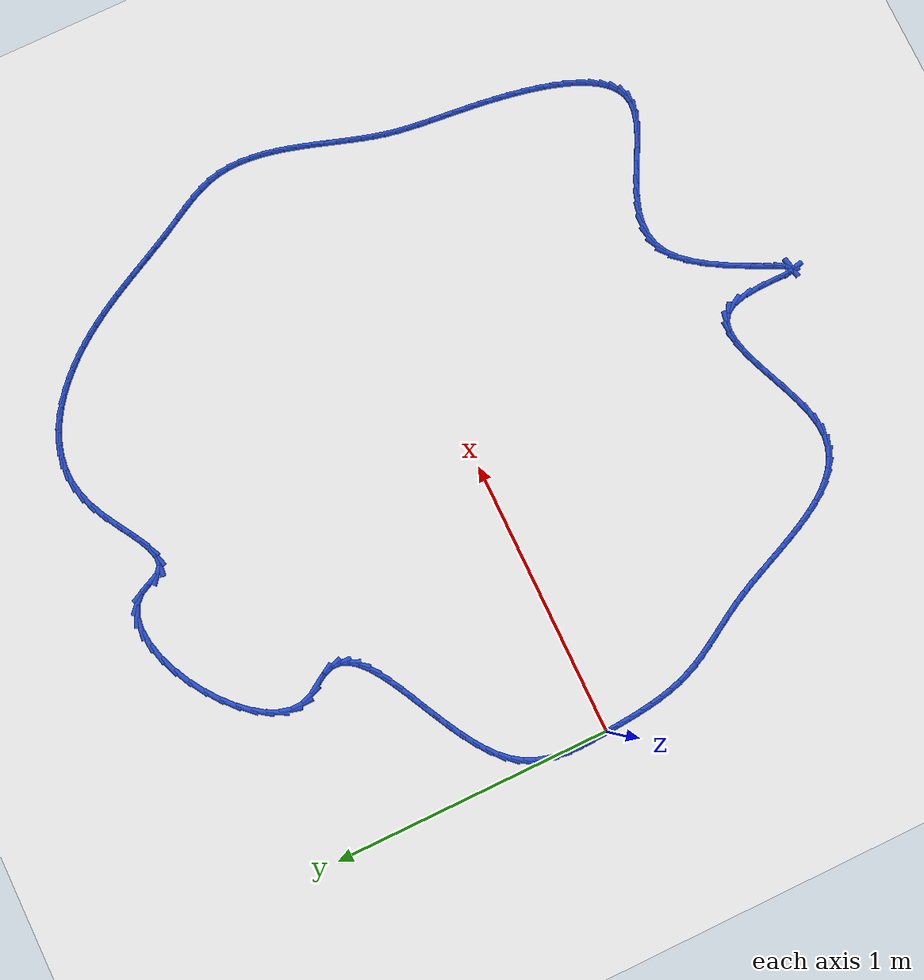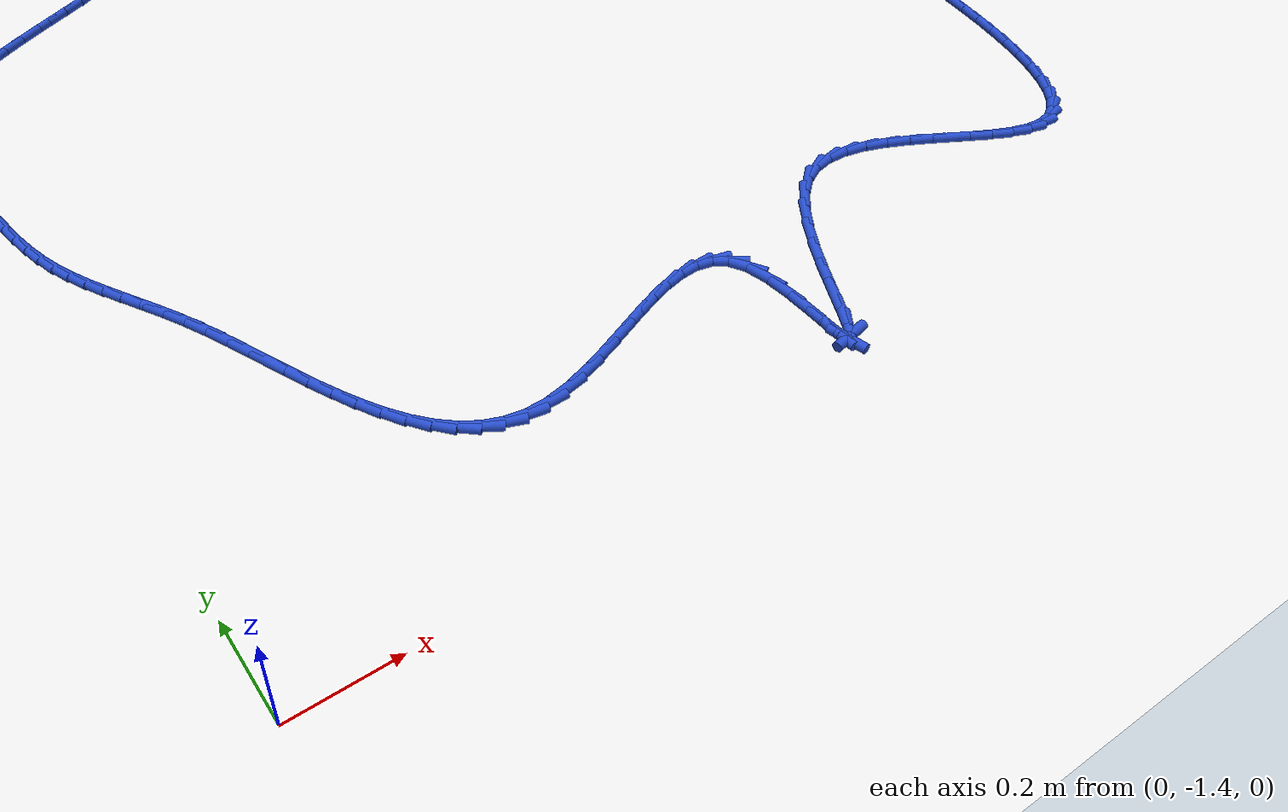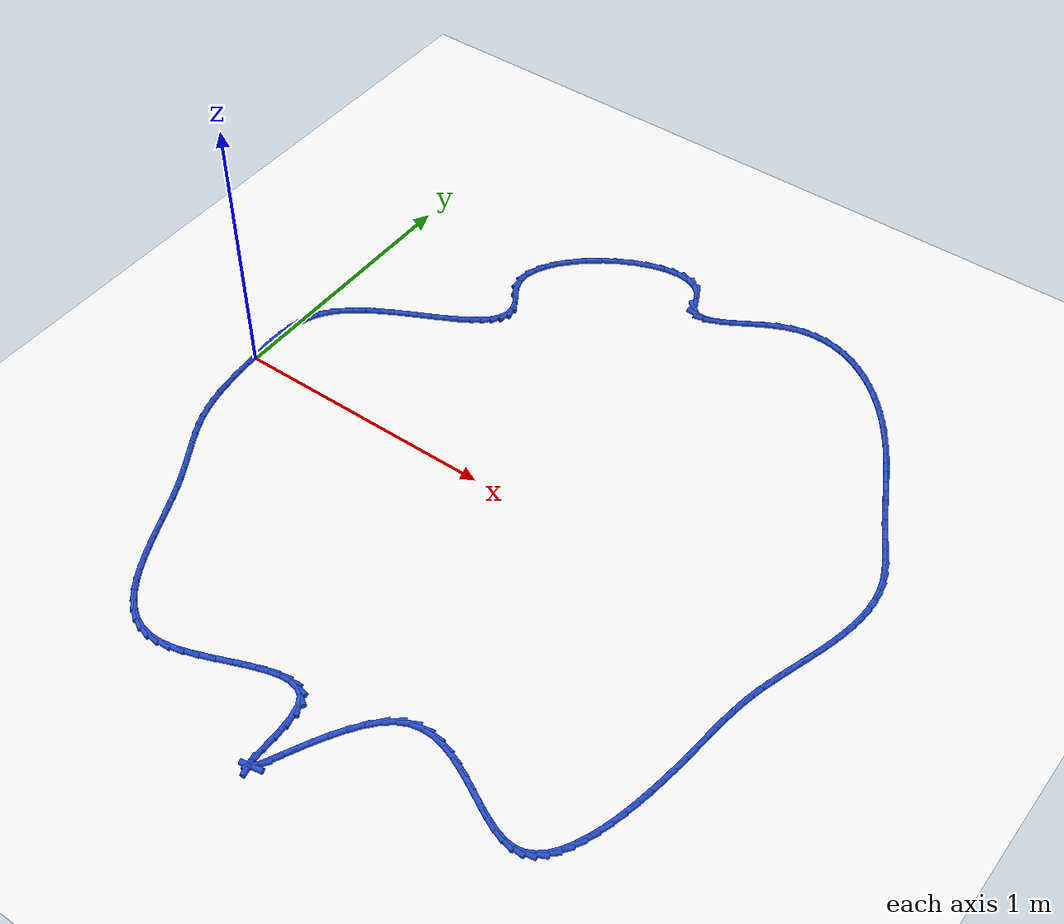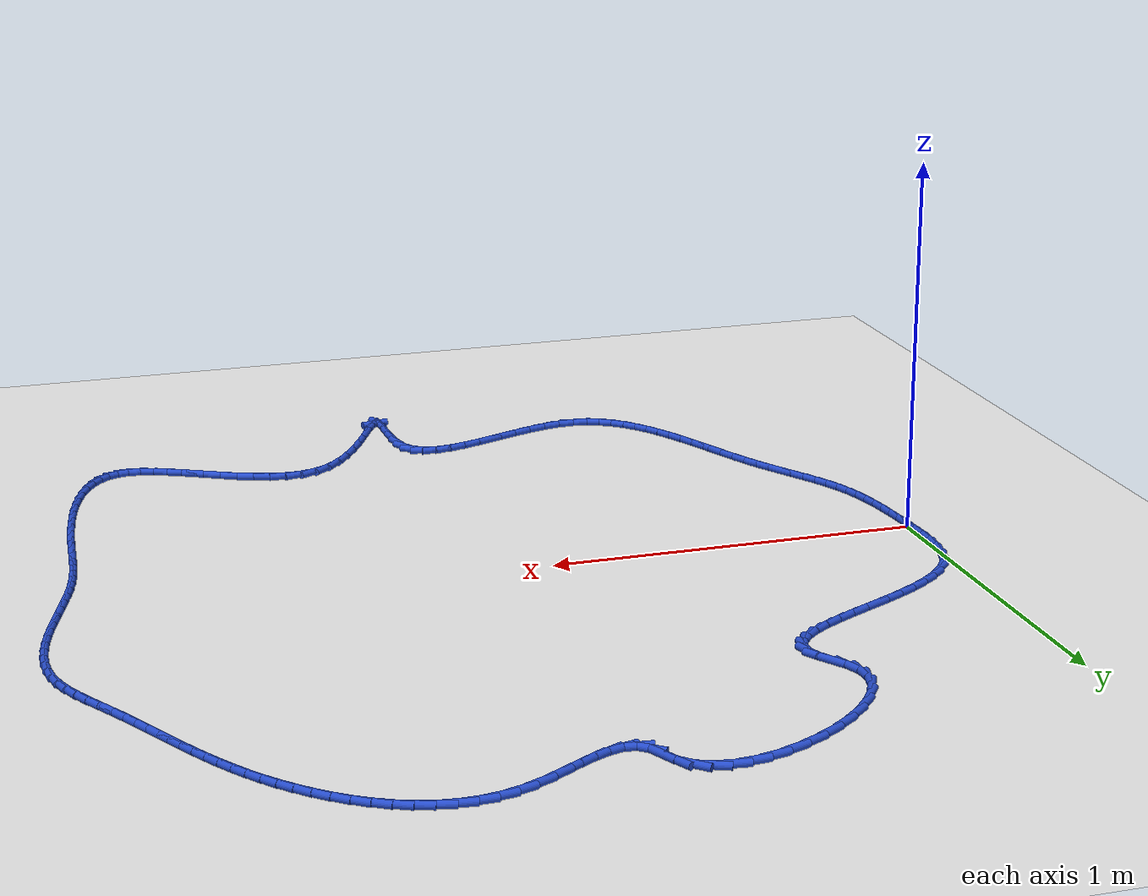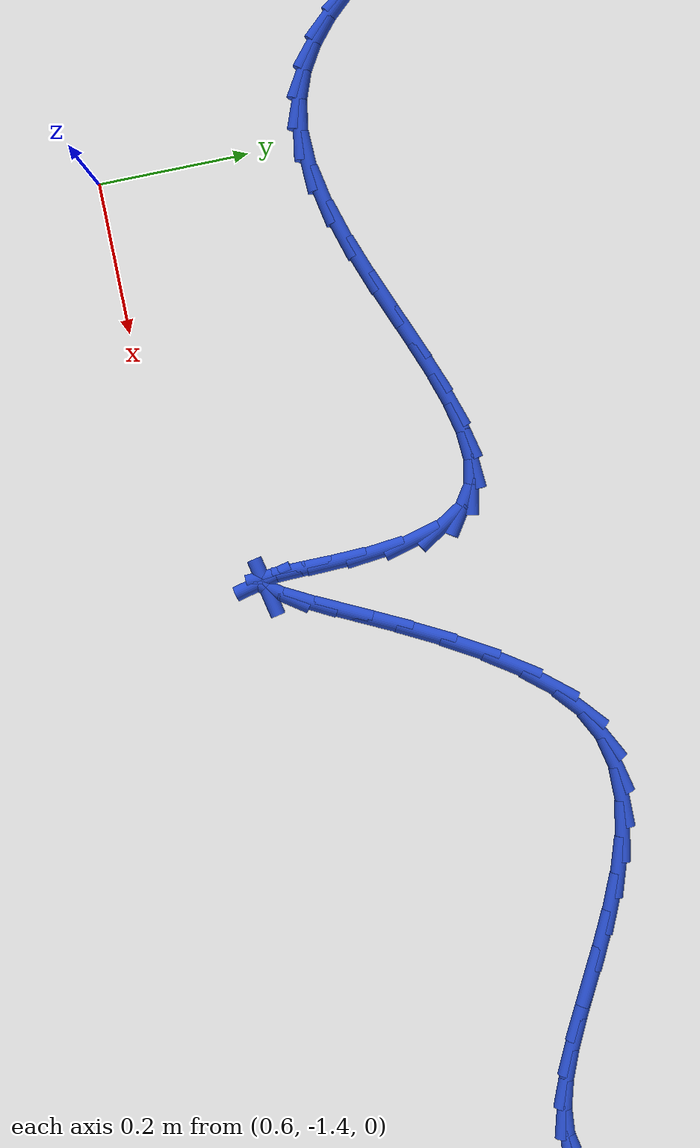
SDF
<sdf version="1.6">
 <world name="default">
  <light name="sun" type="directional">
   <pose>0 0 10 0 -0 0</pose>
   <diffuse>0.8 0.8 0.8 1</diffuse>
   <specular>0.2 0.2 0.2 1</specular>
   <attenuation>
    <range>1000</range>
    <constant>0.9</constant>
    <linear>0.01</linear>
    <quadratic>0.001</quadratic>
   </attenuation>
   <direction>-0.5 0.1 -0.9</direction>
  </light>
  <model name="ground_plane">
   <static>1</static>
   <link name="link">
    <collision name="collision">
     <geometry><plane><normal>0 0 1</normal><size>100 100</size></plane></geometry>
     <surface><friction><ode><mu>100</mu><mu2>50</mu2></ode></friction></surface>
    </collision>
    <visual name="visual">
     <cast_shadows>0</cast_shadows>
     <geometry><plane><normal>0 0 1</normal><size>100 100</size></plane></geometry>
     <material>
      <script><uri>file://media/materials/scripts/gazebo.material</uri><name>Gazebo/WhiteGlow</name></script>
     </material>
    </visual>
   </link>
  </model>
  <gravity>0 0 -9.8</gravity>
  <magnetic_field>6e-06 2.3e-05 -4.2e-05</magnetic_field>
  <atmosphere type="adiabatic"/>
  <physics name="default_physics" default="0" type="ode">
   <max_step_size>0.001</max_step_size>
   <real_time_factor>1</real_time_factor>
   <real_time_update_rate>1000</real_time_update_rate>
  </physics>
  <scene><ambient>0.4 0.4 0.4 1</ambient><background>0.7 0.7 0.7 1</background><shadows>1</shadows></scene>
  <spherical_coordinates>
   <surface_model>EARTH_WGS84</surface_model>
   <latitude_deg>0</latitude_deg>
   <longitude_deg>0</longitude_deg>
   <elevation>0</elevation>
   <heading_deg>0</heading_deg>
  </spherical_coordinates>
  <model name="line">
   <link name="link_0">
    <pose>8.673617379884035e-19 3.469446951953614e-17 0.01 0 1.57 -1.5085652873056417</pose>
    <collision name="collision">
     <geometry><cylinder><radius>0.01</radius><length>0.08</length></cylinder></geometry>
    </collision>
    <visual name="visual">
     <material>
      <script><name>Gazebo/Blue</name><uri>file://media/materials/scripts/gazebo.material</uri></script>
     </material>
     <geometry><cylinder><radius>0.01</radius><length>0.08</length></cylinder></geometry>
    </visual>
   </link>
   <link name="link_1">
    <pose>-0.002795601090388354 0.044864931353532006 0.01 0 1.57 -1.5333618514169722</pose>
    <collision name="collision">
     <geometry><cylinder><radius>0.01</radius><length>0.08</length></cylinder></geometry>
    </collision>
    <visual name="visual">
     <material>
      <script><name>Gazebo/Blue</name><uri>file://media/materials/scripts/gazebo.material</uri></script>
     </material>
     <geometry><cylinder><radius>0.01</radius><length>0.08</length></cylinder></geometry>
    </visual>
   </link>
   <link name="link_2">
    <pose>-0.004472855772627155 0.08964908083377991 0.01 0 1.57 1.5618456030932293</pose>
    <collision name="collision">
     <geometry><cylinder><radius>0.01</radius><length>0.08</length></cylinder></geometry>
    </collision>
    <visual name="visual">
     <material>
      <script><name>Gazebo/Blue</name><uri>file://media/materials/scripts/gazebo.material</uri></script>
     </material>
     <geometry><cylinder><radius>0.01</radius><length>0.08</length></cylinder></geometry>
    </visual>
   </link>
   <link name="link_3">
    <pose>-0.0040761348136489775 0.13397067734941656 0.01 0 1.57 1.492151582347678</pose>
    <collision name="collision">
     <geometry><cylinder><radius>0.01</radius><length>0.08</length></cylinder></geometry>
    </collision>
    <visual name="visual">
     <material>
      <script><name>Gazebo/Blue</name><uri>file://media/materials/scripts/gazebo.material</uri></script>
     </material>
     <geometry><cylinder><radius>0.01</radius><length>0.08</length></cylinder></geometry>
    </visual>
   </link>
   <link name="link_4">
    <pose>-0.0006498089803863884 0.17744794980911469 0.01 0 1.57 1.3971464206757302</pose>
    <collision name="collision">
     <geometry><cylinder><radius>0.01</radius><length>0.08</length></cylinder></geometry>
    </collision>
    <visual name="visual">
     <material>
      <script><name>Gazebo/Blue</name><uri>file://media/materials/scripts/gazebo.material</uri></script>
     </material>
     <geometry><cylinder><radius>0.01</radius><length>0.08</length></cylinder></geometry>
    </visual>
   </link>
   <link name="link_5">
    <pose>0.00676175096022805 0.21969912712154702 0.01 0 1.57 1.2757446567778075</pose>
    <collision name="collision">
     <geometry><cylinder><radius>0.01</radius><length>0.08</length></cylinder></geometry>
    </collision>
    <visual name="visual">
     <material>
      <script><name>Gazebo/Blue</name><uri>file://media/materials/scripts/gazebo.material</uri></script>
     </material>
     <geometry><cylinder><radius>0.01</radius><length>0.08</length></cylinder></geometry>
    </visual>
   </link>
   <link name="link_6">
    <pose>0.019114174241261758 0.2603424381953864 0.01 0 1.57 1.1297058616012565</pose>
    <collision name="collision">
     <geometry><cylinder><radius>0.01</radius><length>0.08</length></cylinder></geometry>
    </collision>
    <visual name="visual">
     <material>
      <script><name>Gazebo/Blue</name><uri>file://media/materials/scripts/gazebo.material</uri></script>
     </material>
     <geometry><cylinder><radius>0.01</radius><length>0.08</length></cylinder></geometry>
    </visual>
   </link>
   <link name="link_7">
    <pose>0.03736309009578216 0.2989961119393055 0.01 0 1.57 0.9657993698622335</pose>
    <collision name="collision">
     <geometry><cylinder><radius>0.01</radius><length>0.08</length></cylinder></geometry>
    </collision>
    <visual name="visual">
     <material>
      <script><name>Gazebo/Blue</name><uri>file://media/materials/scripts/gazebo.material</uri></script>
     </material>
     <geometry><cylinder><radius>0.01</radius><length>0.08</length></cylinder></geometry>
    </visual>
   </link>
   <link name="link_8">
    <pose>0.06245431540034927 0.33528144205125376 0.01 0 1.57 0.8106305641479007</pose>
    <collision name="collision">
     <geometry><cylinder><radius>0.01</radius><length>0.08</length></cylinder></geometry>
    </collision>
    <visual name="visual">
     <material>
      <script><name>Gazebo/Blue</name><uri>file://media/materials/scripts/gazebo.material</uri></script>
     </material>
     <geometry><cylinder><radius>0.01</radius><length>0.08</length></cylinder></geometry>
    </visual>
   </link>
   <link name="link_9">
    <pose>0.0945686016024799 0.36905868259729163 0.01 0 1.57 0.6924659976164941</pose>
    <collision name="collision">
     <geometry><cylinder><radius>0.01</radius><length>0.08</length></cylinder></geometry>
    </collision>
    <visual name="visual">
     <material>
      <script><name>Gazebo/Blue</name><uri>file://media/materials/scripts/gazebo.material</uri></script>
     </material>
     <geometry><cylinder><radius>0.01</radius><length>0.08</length></cylinder></geometry>
    </visual>
   </link>
   <link name="link_10">
    <pose>0.13258652564442144 0.400594183862956 0.01 0 1.57 0.6064123715620233</pose>
    <collision name="collision">
     <geometry><cylinder><radius>0.01</radius><length>0.08</length></cylinder></geometry>
    </collision>
    <visual name="visual">
     <material>
      <script><name>Gazebo/Blue</name><uri>file://media/materials/scripts/gazebo.material</uri></script>
     </material>
     <geometry><cylinder><radius>0.01</radius><length>0.08</length></cylinder></geometry>
    </visual>
   </link>
   <link name="link_11">
    <pose>0.17526230283505712 0.4301937638986017 0.01 0 1.57 0.545457978809259</pose>
    <collision name="collision">
     <geometry><cylinder><radius>0.01</radius><length>0.08</length></cylinder></geometry>
    </collision>
    <visual name="visual">
     <material>
      <script><name>Gazebo/Blue</name><uri>file://media/materials/scripts/gazebo.material</uri></script>
     </material>
     <geometry><cylinder><radius>0.01</radius><length>0.08</length></cylinder></geometry>
    </visual>
   </link>
   <link name="link_12">
    <pose>0.22135014848326998 0.45816324075458364 0.01 0 1.57 0.5045189723497058</pose>
    <collision name="collision">
     <geometry><cylinder><radius>0.01</radius><length>0.08</length></cylinder></geometry>
    </collision>
    <visual name="visual">
     <material>
      <script><name>Gazebo/Blue</name><uri>file://media/materials/scripts/gazebo.material</uri></script>
     </material>
     <geometry><cylinder><radius>0.01</radius><length>0.08</length></cylinder></geometry>
    </visual>
   </link>
   <link name="link_13">
    <pose>0.26960427789794333 0.48480843248125693 0.01 0 1.57 0.48041396956076166</pose>
    <collision name="collision">
     <geometry><cylinder><radius>0.01</radius><length>0.08</length></cylinder></geometry>
    </collision>
    <visual name="visual">
     <material>
      <script><name>Gazebo/Blue</name><uri>file://media/materials/scripts/gazebo.material</uri></script>
     </material>
     <geometry><cylinder><radius>0.01</radius><length>0.08</length></cylinder></geometry>
    </visual>
   </link>
   <link name="link_14">
    <pose>0.31877890638796014 0.510435157128976 0.01 0 1.57 0.47163036350103893</pose>
    <collision name="collision">
     <geometry><cylinder><radius>0.01</radius><length>0.08</length></cylinder></geometry>
    </collision>
    <visual name="visual">
     <material>
      <script><name>Gazebo/Blue</name><uri>file://media/materials/scripts/gazebo.material</uri></script>
     </material>
     <geometry><cylinder><radius>0.01</radius><length>0.08</length></cylinder></geometry>
    </visual>
   </link>
   <link name="link_15">
    <pose>0.36762824926220367 0.5353492327480962 0.01 0 1.57 0.478228815170522</pose>
    <collision name="collision">
     <geometry><cylinder><radius>0.01</radius><length>0.08</length></cylinder></geometry>
    </collision>
    <visual name="visual">
     <material>
      <script><name>Gazebo/Blue</name><uri>file://media/materials/scripts/gazebo.material</uri></script>
     </material>
     <geometry><cylinder><radius>0.01</radius><length>0.08</length></cylinder></geometry>
    </visual>
   </link>
   <link name="link_16">
    <pose>0.4149065218295573 0.5598564773889724 0.01 0 1.57 0.5020217879897807</pose>
    <collision name="collision">
     <geometry><cylinder><radius>0.01</radius><length>0.08</length></cylinder></geometry>
    </collision>
    <visual name="visual">
     <material>
      <script><name>Gazebo/Blue</name><uri>file://media/materials/scripts/gazebo.material</uri></script>
     </material>
     <geometry><cylinder><radius>0.01</radius><length>0.08</length></cylinder></geometry>
    </visual>
   </link>
   <link name="link_17">
    <pose>0.4593679393989038 0.5842627091019592 0.01 0 1.57 0.5471585881664179</pose>
    <collision name="collision">
     <geometry><cylinder><radius>0.01</radius><length>0.08</length></cylinder></geometry>
    </collision>
    <visual name="visual">
     <material>
      <script><name>Gazebo/Blue</name><uri>file://media/materials/scripts/gazebo.material</uri></script>
     </material>
     <geometry><cylinder><radius>0.01</radius><length>0.08</length></cylinder></geometry>
    </visual>
   </link>
   <link name="link_18">
    <pose>0.4997667172791266 0.6088737459374117 0.01 0 1.57 0.6213265562585064</pose>
    <collision name="collision">
     <geometry><cylinder><radius>0.01</radius><length>0.08</length></cylinder></geometry>
    </collision>
    <visual name="visual">
     <material>
      <script><name>Gazebo/Blue</name><uri>file://media/materials/scripts/gazebo.material</uri></script>
     </material>
     <geometry><cylinder><radius>0.01</radius><length>0.08</length></cylinder></geometry>
    </visual>
   </link>
   <link name="link_19">
    <pose>0.5348570707791087 0.6339954059456848 0.01 0 1.57 0.7377412203850204</pose>
    <collision name="collision">
     <geometry><cylinder><radius>0.01</radius><length>0.08</length></cylinder></geometry>
    </collision>
    <visual name="visual">
     <material>
      <script><name>Gazebo/Blue</name><uri>file://media/materials/scripts/gazebo.material</uri></script>
     </material>
     <geometry><cylinder><radius>0.01</radius><length>0.08</length></cylinder></geometry>
    </visual>
   </link>
   <link name="link_20">
    <pose>0.5633932152077336 0.6599335071771335 0.01 0 1.57 0.9169493140732314</pose>
    <collision name="collision">
     <geometry><cylinder><radius>0.01</radius><length>0.08</length></cylinder></geometry>
    </collision>
    <visual name="visual">
     <material>
      <script><name>Gazebo/Blue</name><uri>file://media/materials/scripts/gazebo.material</uri></script>
     </material>
     <geometry><cylinder><radius>0.01</radius><length>0.08</length></cylinder></geometry>
    </visual>
   </link>
   <link name="link_21">
    <pose>0.584129365873884 0.6869938676821125 0.01 0 1.57 1.1813952420875953</pose>
    <collision name="collision">
     <geometry><cylinder><radius>0.01</radius><length>0.08</length></cylinder></geometry>
    </collision>
    <visual name="visual">
     <material>
      <script><name>Gazebo/Blue</name><uri>file://media/materials/scripts/gazebo.material</uri></script>
     </material>
     <geometry><cylinder><radius>0.01</radius><length>0.08</length></cylinder></geometry>
    </visual>
   </link>
   <link name="link_22">
    <pose>0.5958197380864433 0.7154823055109767 0.01 0 1.57 1.5245453806693094</pose>
    <collision name="collision">
     <geometry><cylinder><radius>0.01</radius><length>0.08</length></cylinder></geometry>
    </collision>
    <visual name="visual">
     <material>
      <script><name>Gazebo/Blue</name><uri>file://media/materials/scripts/gazebo.material</uri></script>
     </material>
     <geometry><cylinder><radius>0.01</radius><length>0.08</length></cylinder></geometry>
    </visual>
   </link>
   <link name="link_23">
    <pose>0.5972185471542948 0.7457046387140813 0.01 0 1.57 -1.2663125703326148</pose>
    <collision name="collision">
     <geometry><cylinder><radius>0.01</radius><length>0.08</length></cylinder></geometry>
    </collision>
    <visual name="visual">
     <material>
      <script><name>Gazebo/Blue</name><uri>file://media/materials/scripts/gazebo.material</uri></script>
     </material>
     <geometry><cylinder><radius>0.01</radius><length>0.08</length></cylinder></geometry>
    </visual>
   </link>
   <link name="link_24">
    <pose>0.5870800083863215 0.777966685341781 0.01 0 1.57 -1.0187099531825432</pose>
    <collision name="collision">
     <geometry><cylinder><radius>0.01</radius><length>0.08</length></cylinder></geometry>
    </collision>
    <visual name="visual">
     <material>
      <script><name>Gazebo/Blue</name><uri>file://media/materials/scripts/gazebo.material</uri></script>
     </material>
     <geometry><cylinder><radius>0.01</radius><length>0.08</length></cylinder></geometry>
    </visual>
   </link>
   <link name="link_25">
    <pose>0.5657666882009622 0.8125673808134006 0.01 0 1.57 -1.0012533243651964</pose>
    <collision name="collision">
     <geometry><cylinder><radius>0.01</radius><length>0.08</length></cylinder></geometry>
    </collision>
    <visual name="visual">
     <material>
      <script><name>Gazebo/Blue</name><uri>file://media/materials/scripts/gazebo.material</uri></script>
     </material>
     <geometry><cylinder><radius>0.01</radius><length>0.08</length></cylinder></geometry>
    </visual>
   </link>
   <link name="link_26">
    <pose>0.5419448777534217 0.8497701263460653 0.01 0 1.57 -1.2080535619510553</pose>
    <collision name="collision">
     <geometry><cylinder><radius>0.01</radius><length>0.08</length></cylinder></geometry>
    </collision>
    <visual name="visual">
     <material>
      <script><name>Gazebo/Blue</name><uri>file://media/materials/scripts/gazebo.material</uri></script>
     </material>
     <geometry><cylinder><radius>0.01</radius><length>0.08</length></cylinder></geometry>
    </visual>
   </link>
   <link name="link_27">
    <pose>0.5267493477515651 0.8898070973601989 0.01 0 1.57 -1.5409106943662398</pose>
    <collision name="collision">
     <geometry><cylinder><radius>0.01</radius><length>0.08</length></cylinder></geometry>
    </collision>
    <visual name="visual">
     <material>
      <script><name>Gazebo/Blue</name><uri>file://media/materials/scripts/gazebo.material</uri></script>
     </material>
     <geometry><cylinder><radius>0.01</radius><length>0.08</length></cylinder></geometry>
    </visual>
   </link>
   <link name="link_28">
    <pose>0.5254777672054546 0.9323426520433903 0.01 0 1.57 1.3179245771623167</pose>
    <collision name="collision">
     <geometry><cylinder><radius>0.01</radius><length>0.08</length></cylinder></geometry>
    </collision>
    <visual name="visual">
     <material>
      <script><name>Gazebo/Blue</name><uri>file://media/materials/scripts/gazebo.material</uri></script>
     </material>
     <geometry><cylinder><radius>0.01</radius><length>0.08</length></cylinder></geometry>
    </visual>
   </link>
   <link name="link_29">
    <pose>0.5368630202605317 0.9764026899581894 0.01 0 1.57 1.1046869276985878</pose>
    <collision name="collision">
     <geometry><cylinder><radius>0.01</radius><length>0.08</length></cylinder></geometry>
    </collision>
    <visual name="visual">
     <material>
      <script><name>Gazebo/Blue</name><uri>file://media/materials/scripts/gazebo.material</uri></script>
     </material>
     <geometry><cylinder><radius>0.01</radius><length>0.08</length></cylinder></geometry>
    </visual>
   </link>
   <link name="link_30">
    <pose>0.5592885813045332 1.0209791287959828 0.01 0 1.57 0.9451569806853171</pose>
    <collision name="collision">
     <geometry><cylinder><radius>0.01</radius><length>0.08</length></cylinder></geometry>
    </collision>
    <visual name="visual">
     <material>
      <script><name>Gazebo/Blue</name><uri>file://media/materials/scripts/gazebo.material</uri></script>
     </material>
     <geometry><cylinder><radius>0.01</radius><length>0.08</length></cylinder></geometry>
    </visual>
   </link>
   <link name="link_31">
    <pose>0.5911379247251956 1.0650638862481587 0.01 0 1.57 0.820990334736912</pose>
    <collision name="collision">
     <geometry><cylinder><radius>0.01</radius><length>0.08</length></cylinder></geometry>
    </collision>
    <visual name="visual">
     <material>
      <script><name>Gazebo/Blue</name><uri>file://media/materials/scripts/gazebo.material</uri></script>
     </material>
     <geometry><cylinder><radius>0.01</radius><length>0.08</length></cylinder></geometry>
    </visual>
   </link>
   <link name="link_32">
    <pose>0.6307945249102553 1.1076488800061033 0.01 0 1.57 0.718344709605781</pose>
    <collision name="collision">
     <geometry><cylinder><radius>0.01</radius><length>0.08</length></cylinder></geometry>
    </collision>
    <visual name="visual">
     <material>
      <script><name>Gazebo/Blue</name><uri>file://media/materials/scripts/gazebo.material</uri></script>
     </material>
     <geometry><cylinder><radius>0.01</radius><length>0.08</length></cylinder></geometry>
    </visual>
   </link>
   <link name="link_33">
    <pose>0.6766418562474495 1.1477260277612042 0.01 0 1.57 0.6273810549147172</pose>
    <collision name="collision">
     <geometry><cylinder><radius>0.01</radius><length>0.08</length></cylinder></geometry>
    </collision>
    <visual name="visual">
     <material>
      <script><name>Gazebo/Blue</name><uri>file://media/materials/scripts/gazebo.material</uri></script>
     </material>
     <geometry><cylinder><radius>0.01</radius><length>0.08</length></cylinder></geometry>
    </visual>
   </link>
   <link name="link_34">
    <pose>0.727063393124515 1.1842872472048493 0.01 0 1.57 0.5405528134266864</pose>
    <collision name="collision">
     <geometry><cylinder><radius>0.01</radius><length>0.08</length></cylinder></geometry>
    </collision>
    <visual name="visual">
     <material>
      <script><name>Gazebo/Blue</name><uri>file://media/materials/scripts/gazebo.material</uri></script>
     </material>
     <geometry><cylinder><radius>0.01</radius><length>0.08</length></cylinder></geometry>
    </visual>
   </link>
   <link name="link_35">
    <pose>0.7804426099291873 1.2163244560284252 0.01 0 1.57 0.4510687106434794</pose>
    <collision name="collision">
     <geometry><cylinder><radius>0.01</radius><length>0.08</length></cylinder></geometry>
    </collision>
    <visual name="visual">
     <material>
      <script><name>Gazebo/Blue</name><uri>file://media/materials/scripts/gazebo.material</uri></script>
     </material>
     <geometry><cylinder><radius>0.01</radius><length>0.08</length></cylinder></geometry>
    </visual>
   </link>
   <link name="link_36">
    <pose>0.8351629810492044 1.2428295719233193 0.01 0 1.57 0.3514735164525945</pose>
    <collision name="collision">
     <geometry><cylinder><radius>0.01</radius><length>0.08</length></cylinder></geometry>
    </collision>
    <visual name="visual">
     <material>
      <script><name>Gazebo/Blue</name><uri>file://media/materials/scripts/gazebo.material</uri></script>
     </material>
     <geometry><cylinder><radius>0.01</radius><length>0.08</length></cylinder></geometry>
    </visual>
   </link>
   <link name="link_37">
    <pose>0.889607980872302 1.2627945125809186 0.01 0 1.57 0.23201446020576075</pose>
    <collision name="collision">
     <geometry><cylinder><radius>0.01</radius><length>0.08</length></cylinder></geometry>
    </collision>
    <visual name="visual">
     <material>
      <script><name>Gazebo/Blue</name><uri>file://media/materials/scripts/gazebo.material</uri></script>
     </material>
     <geometry><cylinder><radius>0.01</radius><length>0.08</length></cylinder></geometry>
    </visual>
   </link>
   <link name="link_38">
    <pose>0.942161083786217 1.2752111956926102 0.01 0 1.57 0.07854879735542894</pose>
    <collision name="collision">
     <geometry><cylinder><radius>0.01</radius><length>0.08</length></cylinder></geometry>
    </collision>
    <visual name="visual">
     <material>
      <script><name>Gazebo/Blue</name><uri>file://media/materials/scripts/gazebo.material</uri></script>
     </material>
     <geometry><cylinder><radius>0.01</radius><length>0.08</length></cylinder></geometry>
    </visual>
   </link>
   <link name="link_39">
    <pose>0.9912057641786863 1.279071538949782 0.01 0 1.57 -0.12915216185020603</pose>
    <collision name="collision">
     <geometry><cylinder><radius>0.01</radius><length>0.08</length></cylinder></geometry>
    </collision>
    <visual name="visual">
     <material>
      <script><name>Gazebo/Blue</name><uri>file://media/materials/scripts/gazebo.material</uri></script>
     </material>
     <geometry><cylinder><radius>0.01</radius><length>0.08</length></cylinder></geometry>
    </visual>
   </link>
   <link name="link_40">
    <pose>1.0351254964374463 1.273367460043821 0.01 0 1.57 -0.4126609035056373</pose>
    <collision name="collision">
     <geometry><cylinder><radius>0.01</radius><length>0.08</length></cylinder></geometry>
    </collision>
    <visual name="visual">
     <material>
      <script><name>Gazebo/Blue</name><uri>file://media/materials/scripts/gazebo.material</uri></script>
     </material>
     <geometry><cylinder><radius>0.01</radius><length>0.08</length></cylinder></geometry>
    </visual>
   </link>
   <link name="link_41">
    <pose>1.0723037549502337 1.257090876666114 0.01 0 1.57 -0.7684073377915633</pose>
    <collision name="collision">
     <geometry><cylinder><radius>0.01</radius><length>0.08</length></cylinder></geometry>
    </collision>
    <visual name="visual">
     <material>
      <script><name>Gazebo/Blue</name><uri>file://media/materials/scripts/gazebo.material</uri></script>
     </material>
     <geometry><cylinder><radius>0.01</radius><length>0.08</length></cylinder></geometry>
    </visual>
   </link>
   <link name="link_42">
    <pose>1.1011240141047849 1.2292337065080488 0.01 0 1.57 -1.1052285526028094</pose>
    <collision name="collision">
     <geometry><cylinder><radius>0.01</radius><length>0.08</length></cylinder></geometry>
    </collision>
    <visual name="visual">
     <material>
      <script><name>Gazebo/Blue</name><uri>file://media/materials/scripts/gazebo.material</uri></script>
     </material>
     <geometry><cylinder><radius>0.01</radius><length>0.08</length></cylinder></geometry>
    </visual>
   </link>
   <link name="link_43">
    <pose>1.120776088716246 1.190117511856501 0.01 0 1.57 -1.1345440950313195</pose>
    <collision name="collision">
     <geometry><cylinder><radius>0.01</radius><length>0.08</length></cylinder></geometry>
    </collision>
    <visual name="visual">
     <material>
      <script><name>Gazebo/Blue</name><uri>file://media/materials/scripts/gazebo.material</uri></script>
     </material>
     <geometry><cylinder><radius>0.01</radius><length>0.08</length></cylinder></geometry>
    </visual>
   </link>
   <link name="link_44">
    <pose>1.1381737027840668 1.1528004062209873 0.01 0 1.57 -0.6953278757903961</pose>
    <collision name="collision">
     <geometry><cylinder><radius>0.01</radius><length>0.08</length></cylinder></geometry>
    </collision>
    <visual name="visual">
     <material>
      <script><name>Gazebo/Blue</name><uri>file://media/materials/scripts/gazebo.material</uri></script>
     </material>
     <geometry><cylinder><radius>0.01</radius><length>0.08</length></cylinder></geometry>
    </visual>
   </link>
   <link name="link_45">
    <pose>1.1621259027546067 1.1328162985172405 0.01 0 1.57 -0.09305382350967971</pose>
    <collision name="collision">
     <geometry><cylinder><radius>0.01</radius><length>0.08</length></cylinder></geometry>
    </collision>
    <visual name="visual">
     <material>
      <script><name>Gazebo/Blue</name><uri>file://media/materials/scripts/gazebo.material</uri></script>
     </material>
     <geometry><cylinder><radius>0.01</radius><length>0.08</length></cylinder></geometry>
    </visual>
   </link>
   <link name="link_46">
    <pose>1.1932242339038175 1.1299140983286744 0.01 0 1.57 0.2766016446004508</pose>
    <collision name="collision">
     <geometry><cylinder><radius>0.01</radius><length>0.08</length></cylinder></geometry>
    </collision>
    <visual name="visual">
     <material>
      <script><name>Gazebo/Blue</name><uri>file://media/materials/scripts/gazebo.material</uri></script>
     </material>
     <geometry><cylinder><radius>0.01</radius><length>0.08</length></cylinder></geometry>
    </visual>
   </link>
   <link name="link_47">
    <pose>1.2302846927514741 1.1404347675274107 0.01 0 1.57 0.4514361941164053</pose>
    <collision name="collision">
     <geometry><cylinder><radius>0.01</radius><length>0.08</length></cylinder></geometry>
    </collision>
    <visual name="visual">
     <material>
      <script><name>Gazebo/Blue</name><uri>file://media/materials/scripts/gazebo.material</uri></script>
     </material>
     <geometry><cylinder><radius>0.01</radius><length>0.08</length></cylinder></geometry>
    </visual>
   </link>
   <link name="link_48">
    <pose>1.2721232758173506 1.1607192679855702 0.01 0 1.57 0.5262147834855958</pose>
    <collision name="collision">
     <geometry><cylinder><radius>0.01</radius><length>0.08</length></cylinder></geometry>
    </collision>
    <visual name="visual">
     <material>
      <script><name>Gazebo/Blue</name><uri>file://media/materials/scripts/gazebo.material</uri></script>
     </material>
     <geometry><cylinder><radius>0.01</radius><length>0.08</length></cylinder></geometry>
    </visual>
   </link>
   <link name="link_49">
    <pose>1.3175559796212208 1.187108561575275 0.01 0 1.57 0.5424051947903129</pose>
    <collision name="collision">
     <geometry><cylinder><radius>0.01</radius><length>0.08</length></cylinder></geometry>
    </collision>
    <visual name="visual">
     <material>
      <script><name>Gazebo/Blue</name><uri>file://media/materials/scripts/gazebo.material</uri></script>
     </material>
     <geometry><cylinder><radius>0.01</radius><length>0.08</length></cylinder></geometry>
    </visual>
   </link>
   <link name="link_50">
    <pose>1.36539880068286 1.2159436101686458 0.01 0 1.57 0.5127066067833038</pose>
    <collision name="collision">
     <geometry><cylinder><radius>0.01</radius><length>0.08</length></cylinder></geometry>
    </collision>
    <visual name="visual">
     <material>
      <script><name>Gazebo/Blue</name><uri>file://media/materials/scripts/gazebo.material</uri></script>
     </material>
     <geometry><cylinder><radius>0.01</radius><length>0.08</length></cylinder></geometry>
    </visual>
   </link>
   <link name="link_51">
    <pose>1.414467735522042 1.2435653756378047 0.01 0 1.57 0.43380680264647675</pose>
    <collision name="collision">
     <geometry><cylinder><radius>0.01</radius><length>0.08</length></cylinder></geometry>
    </collision>
    <visual name="visual">
     <material>
      <script><name>Gazebo/Blue</name><uri>file://media/materials/scripts/gazebo.material</uri></script>
     </material>
     <geometry><cylinder><radius>0.01</radius><length>0.08</length></cylinder></geometry>
    </visual>
   </link>
   <link name="link_52">
    <pose>1.4635789488278939 1.2663154872992304 0.01 0 1.57 0.30472834556492473</pose>
    <collision name="collision">
     <geometry><cylinder><radius>0.01</radius><length>0.08</length></cylinder></geometry>
    </collision>
    <visual name="visual">
     <material>
      <script><name>Gazebo/Blue</name><uri>file://media/materials/scripts/gazebo.material</uri></script>
     </material>
     <geometry><cylinder><radius>0.01</radius><length>0.08</length></cylinder></geometry>
    </visual>
   </link>
   <link name="link_53">
    <pose>1.5117860077109255 1.2814777967278073 0.01 0 1.57 0.16167371380117623</pose>
    <collision name="collision">
     <geometry><cylinder><radius>0.01</radius><length>0.08</length></cylinder></geometry>
    </collision>
    <visual name="visual">
     <material>
      <script><name>Gazebo/Blue</name><uri>file://media/materials/scripts/gazebo.material</uri></script>
     </material>
     <geometry><cylinder><radius>0.01</radius><length>0.08</length></cylinder></geometry>
    </visual>
   </link>
   <link name="link_54">
    <pose>1.558852517625105 1.2891542140827497 0.01 0 1.57 0.017828385980663556</pose>
    <collision name="collision">
     <geometry><cylinder><radius>0.01</radius><length>0.08</length></cylinder></geometry>
    </collision>
    <visual name="visual">
     <material>
      <script><name>Gazebo/Blue</name><uri>file://media/materials/scripts/gazebo.material</uri></script>
     </material>
     <geometry><cylinder><radius>0.01</radius><length>0.08</length></cylinder></geometry>
    </visual>
   </link>
   <link name="link_55">
    <pose>1.6046742569499564 1.2899712283025961 0.01 0 1.57 -0.12118348238183992</pose>
    <collision name="collision">
     <geometry><cylinder><radius>0.01</radius><length>0.08</length></cylinder></geometry>
    </collision>
    <visual name="visual">
     <material>
      <script><name>Gazebo/Blue</name><uri>file://media/materials/scripts/gazebo.material</uri></script>
     </material>
     <geometry><cylinder><radius>0.01</radius><length>0.08</length></cylinder></geometry>
    </visual>
   </link>
   <link name="link_56">
    <pose>1.649147004065003 1.2845553283258841 0.01 0 1.57 -0.2508211142694403</pose>
    <collision name="collision">
     <geometry><cylinder><radius>0.01</radius><length>0.08</length></cylinder></geometry>
    </collision>
    <visual name="visual">
     <material>
      <script><name>Gazebo/Blue</name><uri>file://media/materials/scripts/gazebo.material</uri></script>
     </material>
     <geometry><cylinder><radius>0.01</radius><length>0.08</length></cylinder></geometry>
    </visual>
   </link>
   <link name="link_57">
    <pose>1.6921665373497703 1.2735330030911522 0.01 0 1.57 -0.3683352056012104</pose>
    <collision name="collision">
     <geometry><cylinder><radius>0.01</radius><length>0.08</length></cylinder></geometry>
    </collision>
    <visual name="visual">
     <material>
      <script><name>Gazebo/Blue</name><uri>file://media/materials/scripts/gazebo.material</uri></script>
     </material>
     <geometry><cylinder><radius>0.01</radius><length>0.08</length></cylinder></geometry>
    </visual>
   </link>
   <link name="link_58">
    <pose>1.7336286351837813 1.2575307415369381 0.01 0 1.57 -0.4727610839869979</pose>
    <collision name="collision">
     <geometry><cylinder><radius>0.01</radius><length>0.08</length></cylinder></geometry>
    </collision>
    <visual name="visual">
     <material>
      <script><name>Gazebo/Blue</name><uri>file://media/materials/scripts/gazebo.material</uri></script>
     </material>
     <geometry><cylinder><radius>0.01</radius><length>0.08</length></cylinder></geometry>
    </visual>
   </link>
   <link name="link_59">
    <pose>1.7734290759465596 1.2371750326017794 0.01 0 1.57 -0.5644588862308467</pose>
    <collision name="collision">
     <geometry><cylinder><radius>0.01</radius><length>0.08</length></cylinder></geometry>
    </collision>
    <visual name="visual">
     <material>
      <script><name>Gazebo/Blue</name><uri>file://media/materials/scripts/gazebo.material</uri></script>
     </material>
     <geometry><cylinder><radius>0.01</radius><length>0.08</length></cylinder></geometry>
    </visual>
   </link>
   <link name="link_60">
    <pose>1.8114636380176306 1.2130923652242143 0.01 0 1.57 -0.6445583788491225</pose>
    <collision name="collision">
     <geometry><cylinder><radius>0.01</radius><length>0.08</length></cylinder></geometry>
    </collision>
    <visual name="visual">
     <material>
      <script><name>Gazebo/Blue</name><uri>file://media/materials/scripts/gazebo.material</uri></script>
     </material>
     <geometry><cylinder><radius>0.01</radius><length>0.08</length></cylinder></geometry>
    </visual>
   </link>
   <link name="link_61">
    <pose>1.847628099776518 1.1859092283427808 0.01 0 1.57 -0.7145191783988651</pose>
    <collision name="collision">
     <geometry><cylinder><radius>0.01</radius><length>0.08</length></cylinder></geometry>
    </collision>
    <visual name="visual">
     <material>
      <script><name>Gazebo/Blue</name><uri>file://media/materials/scripts/gazebo.material</uri></script>
     </material>
     <geometry><cylinder><radius>0.01</radius><length>0.08</length></cylinder></geometry>
    </visual>
   </link>
   <link name="link_62">
    <pose>1.881818239602745 1.1562521108960164 0.01 0 1.57 -0.7758570601900943</pose>
    <collision name="collision">
     <geometry><cylinder><radius>0.01</radius><length>0.08</length></cylinder></geometry>
    </collision>
    <visual name="visual">
     <material>
      <script><name>Gazebo/Blue</name><uri>file://media/materials/scripts/gazebo.material</uri></script>
     </material>
     <geometry><cylinder><radius>0.01</radius><length>0.08</length></cylinder></geometry>
    </visual>
   </link>
   <link name="link_63">
    <pose>1.9139298358758368 1.1247475018224602 0.01 0 1.57 -0.8300857080220794</pose>
    <collision name="collision">
     <geometry><cylinder><radius>0.01</radius><length>0.08</length></cylinder></geometry>
    </collision>
    <visual name="visual">
     <material>
      <script><name>Gazebo/Blue</name><uri>file://media/materials/scripts/gazebo.material</uri></script>
     </material>
     <geometry><cylinder><radius>0.01</radius><length>0.08</length></cylinder></geometry>
    </visual>
   </link>
   <link name="link_64">
    <pose>1.9438683933005378 1.0920060632692687 0.01 0 1.57 -0.8795188461749557</pose>
    <collision name="collision">
     <geometry><cylinder><radius>0.01</radius><length>0.08</length></cylinder></geometry>
    </collision>
    <visual name="visual">
     <material>
      <script><name>Gazebo/Blue</name><uri>file://media/materials/scripts/gazebo.material</uri></script>
     </material>
     <geometry><cylinder><radius>0.01</radius><length>0.08</length></cylinder></geometry>
    </visual>
   </link>
   <link name="link_65">
    <pose>1.9717119874754243 1.0583576479850987 0.01 0 1.57 -0.9249802212373145</pose>
    <collision name="collision">
     <geometry><cylinder><radius>0.01</radius><length>0.08</length></cylinder></geometry>
    </collision>
    <visual name="visual">
     <material>
      <script><name>Gazebo/Blue</name><uri>file://media/materials/scripts/gazebo.material</uri></script>
     </material>
     <geometry><cylinder><radius>0.01</radius><length>0.08</length></cylinder></geometry>
    </visual>
   </link>
   <link name="link_66">
    <pose>1.9976868856227952 1.0238909695566227 0.01 0 1.57 -0.9659194307792217</pose>
    <collision name="collision">
     <geometry><cylinder><radius>0.01</radius><length>0.08</length></cylinder></geometry>
    </collision>
    <visual name="visual">
     <material>
      <script><name>Gazebo/Blue</name><uri>file://media/materials/scripts/gazebo.material</uri></script>
     </material>
     <geometry><cylinder><radius>0.01</radius><length>0.08</length></cylinder></geometry>
    </visual>
   </link>
   <link name="link_67">
    <pose>2.0220241699544586 0.9886869065626663 0.01 0 1.57 -1.0018791171628585</pose>
    <collision name="collision">
     <geometry><cylinder><radius>0.01</radius><length>0.08</length></cylinder></geometry>
    </collision>
    <visual name="visual">
     <material>
      <script><name>Gazebo/Blue</name><uri>file://media/materials/scripts/gazebo.material</uri></script>
     </material>
     <geometry><cylinder><radius>0.01</radius><length>0.08</length></cylinder></geometry>
    </visual>
   </link>
   <link name="link_68">
    <pose>2.044954922682222 0.9528263375820559 0.01 0 1.57 -1.0325270724326674</pose>
    <collision name="collision">
     <geometry><cylinder><radius>0.01</radius><length>0.08</length></cylinder></geometry>
    </collision>
    <visual name="visual">
     <material>
      <script><name>Gazebo/Blue</name><uri>file://media/materials/scripts/gazebo.material</uri></script>
     </material>
     <geometry><cylinder><radius>0.01</radius><length>0.08</length></cylinder></geometry>
    </visual>
   </link>
   <link name="link_69">
    <pose>2.0667102260178907 0.9163901411936174 0.01 0 1.57 -1.0576403844011244</pose>
    <collision name="collision">
     <geometry><cylinder><radius>0.01</radius><length>0.08</length></cylinder></geometry>
    </collision>
    <visual name="visual">
     <material>
      <script><name>Gazebo/Blue</name><uri>file://media/materials/scripts/gazebo.material</uri></script>
     </material>
     <geometry><cylinder><radius>0.01</radius><length>0.08</length></cylinder></geometry>
    </visual>
   </link>
   <link name="link_70">
    <pose>2.087521162173273 0.8794591959761768 0.01 0 1.57 -1.077085316604985</pose>
    <collision name="collision">
     <geometry><cylinder><radius>0.01</radius><length>0.08</length></cylinder></geometry>
    </collision>
    <visual name="visual">
     <material>
      <script><name>Gazebo/Blue</name><uri>file://media/materials/scripts/gazebo.material</uri></script>
     </material>
     <geometry><cylinder><radius>0.01</radius><length>0.08</length></cylinder></geometry>
    </visual>
   </link>
   <link name="link_71">
    <pose>2.1076188133601756 0.8421143805085595 0.01 0 1.57 -1.0907968812271716</pose>
    <collision name="collision">
     <geometry><cylinder><radius>0.01</radius><length>0.08</length></cylinder></geometry>
    </collision>
    <visual name="visual">
     <material>
      <script><name>Gazebo/Blue</name><uri>file://media/materials/scripts/gazebo.material</uri></script>
     </material>
     <geometry><cylinder><radius>0.01</radius><length>0.08</length></cylinder></geometry>
    </visual>
   </link>
   <link name="link_72">
    <pose>2.127234261790406 0.8044365733695918 0.01 0 1.57 -1.098760964753192</pose>
    <collision name="collision">
     <geometry><cylinder><radius>0.01</radius><length>0.08</length></cylinder></geometry>
    </collision>
    <visual name="visual">
     <material>
      <script><name>Gazebo/Blue</name><uri>file://media/materials/scripts/gazebo.material</uri></script>
     </material>
     <geometry><cylinder><radius>0.01</radius><length>0.08</length></cylinder></geometry>
    </visual>
   </link>
   <link name="link_73">
    <pose>2.1465985896757713 0.7665066531380998 0.01 0 1.57 -1.1010007547661838</pose>
    <collision name="collision">
     <geometry><cylinder><radius>0.01</radius><length>0.08</length></cylinder></geometry>
    </collision>
    <visual name="visual">
     <material>
      <script><name>Gazebo/Blue</name><uri>file://media/materials/scripts/gazebo.material</uri></script>
     </material>
     <geometry><cylinder><radius>0.01</radius><length>0.08</length></cylinder></geometry>
    </visual>
   </link>
   <link name="link_74">
    <pose>2.165942879228078 0.728405498392909 0.01 0 1.57 -1.0975683152265825</pose>
    <collision name="collision">
     <geometry><cylinder><radius>0.01</radius><length>0.08</length></cylinder></geometry>
    </collision>
    <visual name="visual">
     <material>
      <script><name>Gazebo/Blue</name><uri>file://media/materials/scripts/gazebo.material</uri></script>
     </material>
     <geometry><cylinder><radius>0.01</radius><length>0.08</length></cylinder></geometry>
    </visual>
   </link>
   <link name="link_75">
    <pose>2.185498212659134 0.6902139877128455 0.01 0 1.57 -1.08854151376973</pose>
    <collision name="collision">
     <geometry><cylinder><radius>0.01</radius><length>0.08</length></cylinder></geometry>
    </collision>
    <visual name="visual">
     <material>
      <script><name>Gazebo/Blue</name><uri>file://media/materials/scripts/gazebo.material</uri></script>
     </material>
     <geometry><cylinder><radius>0.01</radius><length>0.08</length></cylinder></geometry>
    </visual>
   </link>
   <link name="link_76">
    <pose>2.2054956721807453 0.6520129996767355 0.01 0 1.57 -1.0740260576025773</pose>
    <collision name="collision">
     <geometry><cylinder><radius>0.01</radius><length>0.08</length></cylinder></geometry>
    </collision>
    <visual name="visual">
     <material>
      <script><name>Gazebo/Blue</name><uri>file://media/materials/scripts/gazebo.material</uri></script>
     </material>
     <geometry><cylinder><radius>0.01</radius><length>0.08</length></cylinder></geometry>
    </visual>
   </link>
   <link name="link_77">
    <pose>2.2261663400047205 0.6138834128634045 0.01 0 1.57 -1.057382048069833</pose>
    <collision name="collision">
     <geometry><cylinder><radius>0.01</radius><length>0.08</length></cylinder></geometry>
    </collision>
    <visual name="visual">
     <material>
      <script><name>Gazebo/Blue</name><uri>file://media/materials/scripts/gazebo.material</uri></script>
     </material>
     <geometry><cylinder><radius>0.01</radius><length>0.08</length></cylinder></geometry>
    </visual>
   </link>
   <link name="link_78">
    <pose>2.247596256149327 0.5758769898459094 0.01 0 1.57 -1.058031364144777</pose>
    <collision name="collision">
     <geometry><cylinder><radius>0.01</radius><length>0.08</length></cylinder></geometry>
    </collision>
    <visual name="visual">
     <material>
      <script><name>Gazebo/Blue</name><uri>file://media/materials/scripts/gazebo.material</uri></script>
     </material>
     <geometry><cylinder><radius>0.01</radius><length>0.08</length></cylinder></geometry>
    </visual>
   </link>
   <link name="link_79">
    <pose>2.268994310008976 0.5378694125548293 0.01 0 1.57 -1.0834048588103051</pose>
    <collision name="collision">
     <geometry><cylinder><radius>0.01</radius><length>0.08</length></cylinder></geometry>
    </collision>
    <visual name="visual">
     <material>
      <script><name>Gazebo/Blue</name><uri>file://media/materials/scripts/gazebo.material</uri></script>
     </material>
     <geometry><cylinder><radius>0.01</radius><length>0.08</length></cylinder></geometry>
    </visual>
   </link>
   <link name="link_80">
    <pose>2.2892413380935097 0.499670509051282 0.01 0 1.57 -1.1347647128070406</pose>
    <collision name="collision">
     <geometry><cylinder><radius>0.01</radius><length>0.08</length></cylinder></geometry>
    </collision>
    <visual name="visual">
     <material>
      <script><name>Gazebo/Blue</name><uri>file://media/materials/scripts/gazebo.material</uri></script>
     </material>
     <geometry><cylinder><radius>0.01</radius><length>0.08</length></cylinder></geometry>
    </visual>
   </link>
   <link name="link_81">
    <pose>2.307217606509439 0.4610899928926922 0.01 0 1.57 -1.2141855898034553</pose>
    <collision name="collision">
     <geometry><cylinder><radius>0.01</radius><length>0.08</length></cylinder></geometry>
    </collision>
    <visual name="visual">
     <material>
      <script><name>Gazebo/Blue</name><uri>file://media/materials/scripts/gazebo.material</uri></script>
     </material>
     <geometry><cylinder><radius>0.01</radius><length>0.08</length></cylinder></geometry>
    </visual>
   </link>
   <link name="link_82">
    <pose>2.3218033813632735 0.4219375776364853 0.01 0 1.57 -1.3214065197463125</pose>
    <collision name="collision">
     <geometry><cylinder><radius>0.01</radius><length>0.08</length></cylinder></geometry>
    </collision>
    <visual name="visual">
     <material>
      <script><name>Gazebo/Blue</name><uri>file://media/materials/scripts/gazebo.material</uri></script>
     </material>
     <geometry><cylinder><radius>0.01</radius><length>0.08</length></cylinder></geometry>
    </visual>
   </link>
   <link name="link_83">
    <pose>2.3319652568566966 0.38203890123069356 0.01 0 1.57 -1.4330289292118932</pose>
    <collision name="collision">
     <geometry><cylinder><radius>0.01</radius><length>0.08</length></cylinder></geometry>
    </collision>
    <visual name="visual">
     <material>
      <script><name>Gazebo/Blue</name><uri>file://media/materials/scripts/gazebo.material</uri></script>
     </material>
     <geometry><cylinder><radius>0.01</radius><length>0.08</length></cylinder></geometry>
    </visual>
   </link>
   <link name="link_84">
    <pose>2.3376008645544153 0.3413913441204843 0.01 0 1.57 -1.5326762523684545</pose>
    <collision name="collision">
     <geometry><cylinder><radius>0.01</radius><length>0.08</length></cylinder></geometry>
    </collision>
    <visual name="visual">
     <material>
      <script><name>Gazebo/Blue</name><uri>file://media/materials/scripts/gazebo.material</uri></script>
     </material>
     <geometry><cylinder><radius>0.01</radius><length>0.08</length></cylinder></geometry>
    </visual>
   </link>
   <link name="link_85">
    <pose>2.3391757690565704 0.30009704971928636 0.01 0 1.57 1.522739150454099</pose>
    <collision name="collision">
     <geometry><cylinder><radius>0.01</radius><length>0.08</length></cylinder></geometry>
    </collision>
    <visual name="visual">
     <material>
      <script><name>Gazebo/Blue</name><uri>file://media/materials/scripts/gazebo.material</uri></script>
     </material>
     <geometry><cylinder><radius>0.01</radius><length>0.08</length></cylinder></geometry>
    </visual>
   </link>
   <link name="link_86">
    <pose>2.3371636327671617 0.2582596551905236 0.01 0 1.57 1.4501482491781754</pose>
    <collision name="collision">
     <geometry><cylinder><radius>0.01</radius><length>0.08</length></cylinder></geometry>
    </collision>
    <visual name="visual">
     <material>
      <script><name>Gazebo/Blue</name><uri>file://media/materials/scripts/gazebo.material</uri></script>
     </material>
     <geometry><cylinder><radius>0.01</radius><length>0.08</length></cylinder></geometry>
    </visual>
   </link>
   <link name="link_87">
    <pose>2.332038118090189 0.21598279769761836 0.01 0 1.57 1.3905460015177409</pose>
    <collision name="collision">
     <geometry><cylinder><radius>0.01</radius><length>0.08</length></cylinder></geometry>
    </collision>
    <visual name="visual">
     <material>
      <script><name>Gazebo/Blue</name><uri>file://media/materials/scripts/gazebo.material</uri></script>
     </material>
     <geometry><cylinder><radius>0.01</radius><length>0.08</length></cylinder></geometry>
    </visual>
   </link>
   <link name="link_88">
    <pose>2.3242728874296534 0.17337011440399439 0.01 0 1.57 1.3430225275003047</pose>
    <collision name="collision">
     <geometry><cylinder><radius>0.01</radius><length>0.08</length></cylinder></geometry>
    </collision>
    <visual name="visual">
     <material>
      <script><name>Gazebo/Blue</name><uri>file://media/materials/scripts/gazebo.material</uri></script>
     </material>
     <geometry><cylinder><radius>0.01</radius><length>0.08</length></cylinder></geometry>
    </visual>
   </link>
   <link name="link_89">
    <pose>2.314341603189553 0.1305252424730749 0.01 0 1.57 1.3066323068221963</pose>
    <collision name="collision">
     <geometry><cylinder><radius>0.01</radius><length>0.08</length></cylinder></geometry>
    </collision>
    <visual name="visual">
     <material>
      <script><name>Gazebo/Blue</name><uri>file://media/materials/scripts/gazebo.material</uri></script>
     </material>
     <geometry><cylinder><radius>0.01</radius><length>0.08</length></cylinder></geometry>
    </visual>
   </link>
   <link name="link_90">
    <pose>2.3027179277738887 0.08755181906828365 0.01 0 1.57 1.2805582262021045</pose>
    <collision name="collision">
     <geometry><cylinder><radius>0.01</radius><length>0.08</length></cylinder></geometry>
    </collision>
    <visual name="visual">
     <material>
      <script><name>Gazebo/Blue</name><uri>file://media/materials/scripts/gazebo.material</uri></script>
     </material>
     <geometry><cylinder><radius>0.01</radius><length>0.08</length></cylinder></geometry>
    </visual>
   </link>
   <link name="link_91">
    <pose>2.2898755235866615 0.04455348135304308 0.01 0 1.57 1.2641992245671343</pose>
    <collision name="collision">
     <geometry><cylinder><radius>0.01</radius><length>0.08</length></cylinder></geometry>
    </collision>
    <visual name="visual">
     <material>
      <script><name>Gazebo/Blue</name><uri>file://media/materials/scripts/gazebo.material</uri></script>
     </material>
     <geometry><cylinder><radius>0.01</radius><length>0.08</length></cylinder></geometry>
    </visual>
   </link>
   <link name="link_92">
    <pose>2.276288053031869 0.0016338664907769238 0.01 0 1.57 1.257214986528263</pose>
    <collision name="collision">
     <geometry><cylinder><radius>0.01</radius><length>0.08</length></cylinder></geometry>
    </collision>
    <visual name="visual">
     <material>
      <script><name>Gazebo/Blue</name><uri>file://media/materials/scripts/gazebo.material</uri></script>
     </material>
     <geometry><cylinder><radius>0.01</radius><length>0.08</length></cylinder></geometry>
    </visual>
   </link>
   <link name="link_93">
    <pose>2.262429178513514 -0.04110338835509115 0.01 0 1.57 1.259551061724342</pose>
    <collision name="collision">
     <geometry><cylinder><radius>0.01</radius><length>0.08</length></cylinder></geometry>
    </collision>
    <visual name="visual">
     <material>
      <script><name>Gazebo/Blue</name><uri>file://media/materials/scripts/gazebo.material</uri></script>
     </material>
     <geometry><cylinder><radius>0.01</radius><length>0.08</length></cylinder></geometry>
    </visual>
   </link>
   <link name="link_94">
    <pose>2.2487725624355948 -0.08355464602113874 0.01 0 1.57 1.2714580356318352</pose>
    <collision name="collision">
     <geometry><cylinder><radius>0.01</radius><length>0.08</length></cylinder></geometry>
    </collision>
    <visual name="visual">
     <material>
      <script><name>Gazebo/Blue</name><uri>file://media/materials/scripts/gazebo.material</uri></script>
     </material>
     <geometry><cylinder><radius>0.01</radius><length>0.08</length></cylinder></geometry>
    </visual>
   </link>
   <link name="link_95">
    <pose>2.2357918672021113 -0.1256162693439421 0.01 0 1.57 1.2935102672421779</pose>
    <collision name="collision">
     <geometry><cylinder><radius>0.01</radius><length>0.08</length></cylinder></geometry>
    </collision>
    <visual name="visual">
     <material>
      <script><name>Gazebo/Blue</name><uri>file://media/materials/scripts/gazebo.material</uri></script>
     </material>
     <geometry><cylinder><radius>0.01</radius><length>0.08</length></cylinder></geometry>
    </visual>
   </link>
   <link name="link_96">
    <pose>2.223960755217064 -0.16718462116007796 0.01 0 1.57 1.326618970320532</pose>
    <collision name="collision">
     <geometry><cylinder><radius>0.01</radius><length>0.08</length></cylinder></geometry>
    </collision>
    <visual name="visual">
     <material>
      <script><name>Gazebo/Blue</name><uri>file://media/materials/scripts/gazebo.material</uri></script>
     </material>
     <geometry><cylinder><radius>0.01</radius><length>0.08</length></cylinder></geometry>
    </visual>
   </link>
   <link name="link_97">
    <pose>2.2137527484410637 -0.20815615107561264 0.01 0 1.57 1.368035296951213</pose>
    <collision name="collision">
     <geometry><cylinder><radius>0.01</radius><length>0.08</length></cylinder></geometry>
    </collision>
    <visual name="visual">
     <material>
      <script><name>Gazebo/Blue</name><uri>file://media/materials/scripts/gazebo.material</uri></script>
     </material>
     <geometry><cylinder><radius>0.01</radius><length>0.08</length></cylinder></geometry>
    </visual>
   </link>
   <link name="link_98">
    <pose>2.205449140593209 -0.24854607218185776 0.01 0 1.57 1.40577561578999</pose>
    <collision name="collision">
     <geometry><cylinder><radius>0.01</radius><length>0.08</length></cylinder></geometry>
    </collision>
    <visual name="visual">
     <material>
      <script><name>Gazebo/Blue</name><uri>file://media/materials/scripts/gazebo.material</uri></script>
     </material>
     <geometry><cylinder><radius>0.01</radius><length>0.08</length></cylinder></geometry>
    </visual>
   </link>
   <link name="link_99">
    <pose>2.1987581615484695 -0.28872365095407326 0.01 0 1.57 1.4360628654495673</pose>
    <collision name="collision">
     <geometry><cylinder><radius>0.01</radius><length>0.08</length></cylinder></geometry>
    </collision>
    <visual name="visual">
     <material>
      <script><name>Gazebo/Blue</name><uri>file://media/materials/scripts/gazebo.material</uri></script>
     </material>
     <geometry><cylinder><radius>0.01</radius><length>0.08</length></cylinder></geometry>
    </visual>
   </link>
   <link name="link_100">
    <pose>2.1932817262412145 -0.3291238379354784 0.01 0 1.57 1.4577818361625663</pose>
    <collision name="collision">
     <geometry><cylinder><radius>0.01</radius><length>0.08</length></cylinder></geometry>
    </collision>
    <visual name="visual">
     <material>
      <script><name>Gazebo/Blue</name><uri>file://media/materials/scripts/gazebo.material</uri></script>
     </material>
     <geometry><cylinder><radius>0.01</radius><length>0.08</length></cylinder></geometry>
    </visual>
   </link>
   <link name="link_101">
    <pose>2.1886217496058116 -0.3701815836692933 0.01 0 1.57 1.4705034138745874</pose>
    <collision name="collision">
     <geometry><cylinder><radius>0.01</radius><length>0.08</length></cylinder></geometry>
    </collision>
    <visual name="visual">
     <material>
      <script><name>Gazebo/Blue</name><uri>file://media/materials/scripts/gazebo.material</uri></script>
     </material>
     <geometry><cylinder><radius>0.01</radius><length>0.08</length></cylinder></geometry>
    </visual>
   </link>
   <link name="link_102">
    <pose>2.1843801465766286 -0.412331838698738 0.01 0 1.57 1.4744486940358144</pose>
    <collision name="collision">
     <geometry><cylinder><radius>0.01</radius><length>0.08</length></cylinder></geometry>
    </collision>
    <visual name="visual">
     <material>
      <script><name>Gazebo/Blue</name><uri>file://media/materials/scripts/gazebo.material</uri></script>
     </material>
     <geometry><cylinder><radius>0.01</radius><length>0.08</length></cylinder></geometry>
    </visual>
   </link>
   <link name="link_103">
    <pose>2.1801588320880336 -0.45600955356703265 0.01 0 1.57 1.4703663195500936</pose>
    <collision name="collision">
     <geometry><cylinder><radius>0.01</radius><length>0.08</length></cylinder></geometry>
    </collision>
    <visual name="visual">
     <material>
      <script><name>Gazebo/Blue</name><uri>file://media/materials/scripts/gazebo.material</uri></script>
     </material>
     <geometry><cylinder><radius>0.01</radius><length>0.08</length></cylinder></geometry>
    </visual>
   </link>
   <link name="link_104">
    <pose>2.175559721074396 -0.5016496788173974 0.01 0 1.57 1.4593801011855971</pose>
    <collision name="collision">
     <geometry><cylinder><radius>0.01</radius><length>0.08</length></cylinder></geometry>
    </collision>
    <visual name="visual">
     <material>
      <script><name>Gazebo/Blue</name><uri>file://media/materials/scripts/gazebo.material</uri></script>
     </material>
     <geometry><cylinder><radius>0.01</radius><length>0.08</length></cylinder></geometry>
    </visual>
   </link>
   <link name="link_105">
    <pose>2.170186310061598 -0.5496782145809687 0.01 0 1.57 1.4432663799408116</pose>
    <collision name="collision">
     <geometry><cylinder><radius>0.01</radius><length>0.08</length></cylinder></geometry>
    </collision>
    <visual name="visual">
     <material>
      <script><name>Gazebo/Blue</name><uri>file://media/materials/scripts/gazebo.material</uri></script>
     </material>
     <geometry><cylinder><radius>0.01</radius><length>0.08</length></cylinder></geometry>
    </visual>
   </link>
   <link name="link_106">
    <pose>2.1637326147115408 -0.6000089025704309 0.01 0 1.57 1.423094093432509</pose>
    <collision name="collision">
     <geometry><cylinder><radius>0.01</radius><length>0.08</length></cylinder></geometry>
    </collision>
    <visual name="visual">
     <material>
      <script><name>Gazebo/Blue</name><uri>file://media/materials/scripts/gazebo.material</uri></script>
     </material>
     <geometry><cylinder><radius>0.01</radius><length>0.08</length></cylinder></geometry>
    </visual>
   </link>
   <link name="link_107">
    <pose>2.156030495178369 -0.6517754063326643 0.01 0 1.57 1.3982974494526113</pose>
    <collision name="collision">
     <geometry><cylinder><radius>0.01</radius><length>0.08</length></cylinder></geometry>
    </collision>
    <visual name="visual">
     <material>
      <script><name>Gazebo/Blue</name><uri>file://media/materials/scripts/gazebo.material</uri></script>
     </material>
     <geometry><cylinder><radius>0.01</radius><length>0.08</length></cylinder></geometry>
    </visual>
   </link>
   <link name="link_108">
    <pose>2.1469233862590675 -0.7040458871517635 0.01 0 1.57 1.3678402469636062</pose>
    <collision name="collision">
     <geometry><cylinder><radius>0.01</radius><length>0.08</length></cylinder></geometry>
    </collision>
    <visual name="visual">
     <material>
      <script><name>Gazebo/Blue</name><uri>file://media/materials/scripts/gazebo.material</uri></script>
     </material>
     <geometry><cylinder><radius>0.01</radius><length>0.08</length></cylinder></geometry>
    </visual>
   </link>
   <link name="link_109">
    <pose>2.1362547227506203 -0.7558885063118242 0.01 0 1.57 1.3301839681043932</pose>
    <collision name="collision">
     <geometry><cylinder><radius>0.01</radius><length>0.08</length></cylinder></geometry>
    </collision>
    <visual name="visual">
     <material>
      <script><name>Gazebo/Blue</name><uri>file://media/materials/scripts/gazebo.material</uri></script>
     </material>
     <geometry><cylinder><radius>0.01</radius><length>0.08</length></cylinder></geometry>
    </visual>
   </link>
   <link name="link_110">
    <pose>2.1238679394500135 -0.8063714250969415 0.01 0 1.57 1.2830739590966878</pose>
    <collision name="collision">
     <geometry><cylinder><radius>0.01</radius><length>0.08</length></cylinder></geometry>
    </collision>
    <visual name="visual">
     <material>
      <script><name>Gazebo/Blue</name><uri>file://media/materials/scripts/gazebo.material</uri></script>
     </material>
     <geometry><cylinder><radius>0.01</radius><length>0.08</length></cylinder></geometry>
    </visual>
   </link>
   <link name="link_111">
    <pose>2.109606471154231 -0.8545628047912105 0.01 0 1.57 1.223190171035051</pose>
    <collision name="collision">
     <geometry><cylinder><radius>0.01</radius><length>0.08</length></cylinder></geometry>
    </collision>
    <visual name="visual">
     <material>
      <script><name>Gazebo/Blue</name><uri>file://media/materials/scripts/gazebo.material</uri></script>
     </material>
     <geometry><cylinder><radius>0.01</radius><length>0.08</length></cylinder></geometry>
    </visual>
   </link>
   <link name="link_112">
    <pose>2.093313752660257 -0.8995308066787254 0.01 0 1.57 1.1456060980238354</pose>
    <collision name="collision">
     <geometry><cylinder><radius>0.01</radius><length>0.08</length></cylinder></geometry>
    </collision>
    <visual name="visual">
     <material>
      <script><name>Gazebo/Blue</name><uri>file://media/materials/scripts/gazebo.material</uri></script>
     </material>
     <geometry><cylinder><radius>0.01</radius><length>0.08</length></cylinder></geometry>
    </visual>
   </link>
   <link name="link_113">
    <pose>2.074833218765076 -0.9403435920435832 0.01 0 1.57 1.043037182448613</pose>
    <collision name="collision">
     <geometry><cylinder><radius>0.01</radius><length>0.08</length></cylinder></geometry>
    </collision>
    <visual name="visual">
     <material>
      <script><name>Gazebo/Blue</name><uri>file://media/materials/scripts/gazebo.material</uri></script>
     </material>
     <geometry><cylinder><radius>0.01</radius><length>0.08</length></cylinder></geometry>
    </visual>
   </link>
   <link name="link_114">
    <pose>2.0540083042656736 -0.9760693221698784 0.01 0 1.57 0.9051440557734386</pose>
    <collision name="collision">
     <geometry><cylinder><radius>0.01</radius><length>0.08</length></cylinder></geometry>
    </collision>
    <visual name="visual">
     <material>
      <script><name>Gazebo/Blue</name><uri>file://media/materials/scripts/gazebo.material</uri></script>
     </material>
     <geometry><cylinder><radius>0.01</radius><length>0.08</length></cylinder></geometry>
    </visual>
   </link>
   <link name="link_115">
    <pose>2.0306824439590336 -1.0057761583417062 0.01 0 1.57 0.7192800184675576</pose>
    <collision name="collision">
     <geometry><cylinder><radius>0.01</radius><length>0.08</length></cylinder></geometry>
    </collision>
    <visual name="visual">
     <material>
      <script><name>Gazebo/Blue</name><uri>file://media/materials/scripts/gazebo.material</uri></script>
     </material>
     <geometry><cylinder><radius>0.01</radius><length>0.08</length></cylinder></geometry>
    </visual>
   </link>
   <link name="link_116">
    <pose>2.0046990726421408 -1.0285322618431614 0.01 0 1.57 0.4767507269996236</pose>
    <collision name="collision">
     <geometry><cylinder><radius>0.01</radius><length>0.08</length></cylinder></geometry>
    </collision>
    <visual name="visual">
     <material>
      <script><name>Gazebo/Blue</name><uri>file://media/materials/scripts/gazebo.material</uri></script>
     </material>
     <geometry><cylinder><radius>0.01</radius><length>0.08</length></cylinder></geometry>
    </visual>
   </link>
   <link name="link_117">
    <pose>1.9759016251119788 -1.0434057939583392 0.01 0 1.57 0.18859430125559815</pose>
    <collision name="collision">
     <geometry><cylinder><radius>0.01</radius><length>0.08</length></cylinder></geometry>
    </collision>
    <visual name="visual">
     <material>
      <script><name>Gazebo/Blue</name><uri>file://media/materials/scripts/gazebo.material</uri></script>
     </material>
     <geometry><cylinder><radius>0.01</radius><length>0.08</length></cylinder></geometry>
    </visual>
   </link>
   <link name="link_118">
    <pose>1.9441343803120743 -1.0494689709691845 0.01 0 1.57 -0.08357877627296459</pose>
    <collision name="collision">
     <geometry><cylinder><radius>0.01</radius><length>0.08</length></cylinder></geometry>
    </collision>
    <visual name="visual">
     <material>
      <script><name>Gazebo/Blue</name><uri>file://media/materials/scripts/gazebo.material</uri></script>
     </material>
     <geometry><cylinder><radius>0.01</radius><length>0.08</length></cylinder></geometry>
    </visual>
   </link>
   <link name="link_119">
    <pose>1.909400912750167 -1.0465592118086304 0.01 0 1.57 -0.27112683690852524</pose>
    <collision name="collision">
     <geometry><cylinder><radius>0.01</radius><length>0.08</length></cylinder></geometry>
    </collision>
    <visual name="visual">
     <material>
      <script><name>Gazebo/Blue</name><uri>file://media/materials/scripts/gazebo.material</uri></script>
     </material>
     <geometry><cylinder><radius>0.01</radius><length>0.08</length></cylinder></geometry>
    </visual>
   </link>
   <link name="link_120">
    <pose>1.872051003371539 -1.0361769954269848 0.01 0 1.57 -0.3871856117185208</pose>
    <collision name="collision">
     <geometry><cylinder><radius>0.01</radius><length>0.08</length></cylinder></geometry>
    </collision>
    <visual name="visual">
     <material>
      <script><name>Gazebo/Blue</name><uri>file://media/materials/scripts/gazebo.material</uri></script>
     </material>
     <geometry><cylinder><radius>0.01</radius><length>0.08</length></cylinder></geometry>
    </visual>
   </link>
   <link name="link_121">
    <pose>1.8324798832300428 -1.02004112790587 0.01 0 1.57 -0.45339520669194533</pose>
    <collision name="collision">
     <geometry><cylinder><radius>0.01</radius><length>0.08</length></cylinder></geometry>
    </collision>
    <visual name="visual">
     <material>
      <script><name>Gazebo/Blue</name><uri>file://media/materials/scripts/gazebo.material</uri></script>
     </material>
     <geometry><cylinder><radius>0.01</radius><length>0.08</length></cylinder></geometry>
    </visual>
   </link>
   <link name="link_122">
    <pose>1.7910827833795309 -0.9998704153269088 0.01 0 1.57 -0.4834860086576357</pose>
    <collision name="collision">
     <geometry><cylinder><radius>0.01</radius><length>0.08</length></cylinder></geometry>
    </collision>
    <visual name="visual">
     <material>
      <script><name>Gazebo/Blue</name><uri>file://media/materials/scripts/gazebo.material</uri></script>
     </material>
     <geometry><cylinder><radius>0.01</radius><length>0.08</length></cylinder></geometry>
    </visual>
   </link>
   <link name="link_123">
    <pose>1.7482549348738565 -0.9773836637717243 0.01 0 1.57 -0.48444226378448535</pose>
    <collision name="collision">
     <geometry><cylinder><radius>0.01</radius><length>0.08</length></cylinder></geometry>
    </collision>
    <visual name="visual">
     <material>
      <script><name>Gazebo/Blue</name><uri>file://media/materials/scripts/gazebo.material</uri></script>
     </material>
     <geometry><cylinder><radius>0.01</radius><length>0.08</length></cylinder></geometry>
    </visual>
   </link>
   <link name="link_124">
    <pose>1.704391568766872 -0.9542996793219389 0.01 0 1.57 -0.45843154738219094</pose>
    <collision name="collision">
     <geometry><cylinder><radius>0.01</radius><length>0.08</length></cylinder></geometry>
    </collision>
    <visual name="visual">
     <material>
      <script><name>Gazebo/Blue</name><uri>file://media/materials/scripts/gazebo.material</uri></script>
     </material>
     <geometry><cylinder><radius>0.01</radius><length>0.08</length></cylinder></geometry>
    </visual>
   </link>
   <link name="link_125">
    <pose>1.659887916112431 -0.9323372680591762 0.01 0 1.57 -0.4038343311286169</pose>
    <collision name="collision">
     <geometry><cylinder><radius>0.01</radius><length>0.08</length></cylinder></geometry>
    </collision>
    <visual name="visual">
     <material>
      <script><name>Gazebo/Blue</name><uri>file://media/materials/scripts/gazebo.material</uri></script>
     </material>
     <geometry><cylinder><radius>0.01</radius><length>0.08</length></cylinder></geometry>
    </visual>
   </link>
   <link name="link_126">
    <pose>1.6151392079643845 -0.9132152360650582 0.01 0 1.57 -0.31561688773560503</pose>
    <collision name="collision">
     <geometry><cylinder><radius>0.01</radius><length>0.08</length></cylinder></geometry>
    </collision>
    <visual name="visual">
     <material>
      <script><name>Gazebo/Blue</name><uri>file://media/materials/scripts/gazebo.material</uri></script>
     </material>
     <geometry><cylinder><radius>0.01</radius><length>0.08</length></cylinder></geometry>
    </visual>
   </link>
   <link name="link_127">
    <pose>1.5705406753765867 -0.8986523894212078 0.01 0 1.57 -0.18589379476761916</pose>
    <collision name="collision">
     <geometry><cylinder><radius>0.01</radius><length>0.08</length></cylinder></geometry>
    </collision>
    <visual name="visual">
     <material>
      <script><name>Gazebo/Blue</name><uri>file://media/materials/scripts/gazebo.material</uri></script>
     </material>
     <geometry><cylinder><radius>0.01</radius><length>0.08</length></cylinder></geometry>
    </visual>
   </link>
   <link name="link_128">
    <pose>1.526487549402889 -0.8903675342092481 0.01 0 1.57 -0.00668143786870774</pose>
    <collision name="collision">
     <geometry><cylinder><radius>0.01</radius><length>0.08</length></cylinder></geometry>
    </collision>
    <visual name="visual">
     <material>
      <script><name>Gazebo/Blue</name><uri>file://media/materials/scripts/gazebo.material</uri></script>
     </material>
     <geometry><cylinder><radius>0.01</radius><length>0.08</length></cylinder></geometry>
    </visual>
   </link>
   <link name="link_129">
    <pose>1.4833750610971452 -0.8900794765108018 0.01 0 1.57 0.22194787900194207</pose>
    <collision name="collision">
     <geometry><cylinder><radius>0.01</radius><length>0.08</length></cylinder></geometry>
    </collision>
    <visual name="visual">
     <material>
      <script><name>Gazebo/Blue</name><uri>file://media/materials/scripts/gazebo.material</uri></script>
     </material>
     <geometry><cylinder><radius>0.01</radius><length>0.08</length></cylinder></geometry>
    </visual>
   </link>
   <link name="link_130">
    <pose>1.4415984415132082 -0.8995070224074918 0.01 0 1.57 0.480271120695891</pose>
    <collision name="collision">
     <geometry><cylinder><radius>0.01</radius><length>0.08</length></cylinder></geometry>
    </collision>
    <visual name="visual">
     <material>
      <script><name>Gazebo/Blue</name><uri>file://media/materials/scripts/gazebo.material</uri></script>
     </material>
     <geometry><cylinder><radius>0.01</radius><length>0.08</length></cylinder></geometry>
    </visual>
   </link>
   <link name="link_131">
    <pose>1.4015529209863633 -0.9203689564528582 0.01 0 1.57 0.7172910151306218</pose>
    <collision name="collision">
     <geometry><cylinder><radius>0.01</radius><length>0.08</length></cylinder></geometry>
    </collision>
    <visual name="visual">
     <material>
      <script><name>Gazebo/Blue</name><uri>file://media/materials/scripts/gazebo.material</uri></script>
     </material>
     <geometry><cylinder><radius>0.01</radius><length>0.08</length></cylinder></geometry>
    </visual>
   </link>
   <link name="link_132">
    <pose>1.3636032838658634 -0.9534719081359347 0.01 0 1.57 0.8770985088369492</pose>
    <collision name="collision">
     <geometry><cylinder><radius>0.01</radius><length>0.08</length></cylinder></geometry>
    </collision>
    <visual name="visual">
     <material>
      <script><name>Gazebo/Blue</name><uri>file://media/materials/scripts/gazebo.material</uri></script>
     </material>
     <geometry><cylinder><radius>0.01</radius><length>0.08</length></cylinder></geometry>
    </visual>
   </link>
   <link name="link_133">
    <pose>1.3280028457100588 -0.9962829264167529 0.01 0 1.57 0.9798637773802102</pose>
    <collision name="collision">
     <geometry><cylinder><radius>0.01</radius><length>0.08</length></cylinder></geometry>
    </collision>
    <visual name="visual">
     <material>
      <script><name>Gazebo/Blue</name><uri>file://media/materials/scripts/gazebo.material</uri></script>
     </material>
     <geometry><cylinder><radius>0.01</radius><length>0.08</length></cylinder></geometry>
    </visual>
   </link>
   <link name="link_134">
    <pose>1.2949794186230337 -1.045504982358611 0.01 0 1.57 1.0471636905410215</pose>
    <collision name="collision">
     <geometry><cylinder><radius>0.01</radius><length>0.08</length></cylinder></geometry>
    </collision>
    <visual name="visual">
     <material>
      <script><name>Gazebo/Blue</name><uri>file://media/materials/scripts/gazebo.material</uri></script>
     </material>
     <geometry><cylinder><radius>0.01</radius><length>0.08</length></cylinder></geometry>
    </visual>
   </link>
   <link name="link_135">
    <pose>1.2647608147088722 -1.0978410470248072 0.01 0 1.57 1.0902755903725512</pose>
    <collision name="collision">
     <geometry><cylinder><radius>0.01</radius><length>0.08</length></cylinder></geometry>
    </collision>
    <visual name="visual">
     <material>
      <script><name>Gazebo/Blue</name><uri>file://media/materials/scripts/gazebo.material</uri></script>
     </material>
     <geometry><cylinder><radius>0.01</radius><length>0.08</length></cylinder></geometry>
    </visual>
   </link>
   <link name="link_136">
    <pose>1.2375748460716567 -1.149994091478641 0.01 0 1.57 1.1139264036140566</pose>
    <collision name="collision">
     <geometry><cylinder><radius>0.01</radius><length>0.08</length></cylinder></geometry>
    </collision>
    <visual name="visual">
     <material>
      <script><name>Gazebo/Blue</name><uri>file://media/materials/scripts/gazebo.material</uri></script>
     </material>
     <geometry><cylinder><radius>0.01</radius><length>0.08</length></cylinder></geometry>
    </visual>
   </link>
   <link name="link_137">
    <pose>1.2136493248154714 -1.1986670867834104 0.01 0 1.57 1.116947910351331</pose>
    <collision name="collision">
     <geometry><cylinder><radius>0.01</radius><length>0.08</length></cylinder></geometry>
    </collision>
    <visual name="visual">
     <material>
      <script><name>Gazebo/Blue</name><uri>file://media/materials/scripts/gazebo.material</uri></script>
     </material>
     <geometry><cylinder><radius>0.01</radius><length>0.08</length></cylinder></geometry>
    </visual>
   </link>
   <link name="link_138">
    <pose>1.1932120630443985 -1.2405630040024136 0.01 0 1.57 1.0869862791659575</pose>
    <collision name="collision">
     <geometry><cylinder><radius>0.01</radius><length>0.08</length></cylinder></geometry>
    </collision>
    <visual name="visual">
     <material>
      <script><name>Gazebo/Blue</name><uri>file://media/materials/scripts/gazebo.material</uri></script>
     </material>
     <geometry><cylinder><radius>0.01</radius><length>0.08</length></cylinder></geometry>
    </visual>
   </link>
   <link name="link_139">
    <pose>1.1764908728625227 -1.2723848141989493 0.01 0 1.57 0.9651138145452144</pose>
    <collision name="collision">
     <geometry><cylinder><radius>0.01</radius><length>0.08</length></cylinder></geometry>
    </collision>
    <visual name="visual">
     <material>
      <script><name>Gazebo/Blue</name><uri>file://media/materials/scripts/gazebo.material</uri></script>
     </material>
     <geometry><cylinder><radius>0.01</radius><length>0.08</length></cylinder></geometry>
    </visual>
   </link>
   <link name="link_140">
    <pose>1.1637135663739264 -1.2908354884363171 0.01 0 1.57 0.20424508810851663</pose>
    <collision name="collision">
     <geometry><cylinder><radius>0.01</radius><length>0.08</length></cylinder></geometry>
    </collision>
    <visual name="visual">
     <material>
      <script><name>Gazebo/Blue</name><uri>file://media/materials/scripts/gazebo.material</uri></script>
     </material>
     <geometry><cylinder><radius>0.01</radius><length>0.08</length></cylinder></geometry>
    </visual>
   </link>
   <link name="link_141">
    <pose>1.155107955682693 -1.2926179977778152 0.01 0 1.57 -1.333927067120925</pose>
    <collision name="collision">
     <geometry><cylinder><radius>0.01</radius><length>0.08</length></cylinder></geometry>
    </collision>
    <visual name="visual">
     <material>
      <script><name>Gazebo/Blue</name><uri>file://media/materials/scripts/gazebo.material</uri></script>
     </material>
     <geometry><cylinder><radius>0.01</radius><length>0.08</length></cylinder></geometry>
    </visual>
   </link>
   <link name="link_142">
    <pose>1.150806997937086 -1.2748013454733287 0.01 0 1.57 -1.5365008615518945</pose>
    <collision name="collision">
     <geometry><cylinder><radius>0.01</radius><length>0.08</length></cylinder></geometry>
    </collision>
    <visual name="visual">
     <material>
      <script><name>Gazebo/Blue</name><uri>file://media/materials/scripts/gazebo.material</uri></script>
     </material>
     <geometry><cylinder><radius>0.01</radius><length>0.08</length></cylinder></geometry>
    </visual>
   </link>
   <link name="link_143">
    <pose>1.149600558940589 -1.2396373389548523 0.01 0 1.57 -1.5639382713969874</pose>
    <collision name="collision">
     <geometry><cylinder><radius>0.01</radius><length>0.08</length></cylinder></geometry>
    </collision>
    <visual name="visual">
     <material>
      <script><name>Gazebo/Blue</name><uri>file://media/materials/scripts/gazebo.material</uri></script>
     </material>
     <geometry><cylinder><radius>0.01</radius><length>0.08</length></cylinder></geometry>
    </visual>
   </link>
   <link name="link_144">
    <pose>1.14928223666944 -1.1932222457364223 0.01 0 1.57 -1.538558429131092</pose>
    <collision name="collision">
     <geometry><cylinder><radius>0.01</radius><length>0.08</length></cylinder></geometry>
    </collision>
    <visual name="visual">
     <material>
      <script><name>Gazebo/Blue</name><uri>file://media/materials/scripts/gazebo.material</uri></script>
     </material>
     <geometry><cylinder><radius>0.01</radius><length>0.08</length></cylinder></geometry>
    </visual>
   </link>
   <link name="link_145">
    <pose>1.147622084886745 -1.141743187201961 0.01 0 1.57 -1.4672687945599394</pose>
    <collision name="collision">
     <geometry><cylinder><radius>0.01</radius><length>0.08</length></cylinder></geometry>
    </collision>
    <visual name="visual">
     <material>
      <script><name>Gazebo/Blue</name><uri>file://media/materials/scripts/gazebo.material</uri></script>
     </material>
     <geometry><cylinder><radius>0.01</radius><length>0.08</length></cylinder></geometry>
    </visual>
   </link>
   <link name="link_146">
    <pose>1.1423901573556112 -1.091387284735388 0.01 0 1.57 -1.3198740815628909</pose>
    <collision name="collision">
     <geometry><cylinder><radius>0.01</radius><length>0.08</length></cylinder></geometry>
    </collision>
    <visual name="visual">
     <material>
      <script><name>Gazebo/Blue</name><uri>file://media/materials/scripts/gazebo.material</uri></script>
     </material>
     <geometry><cylinder><radius>0.01</radius><length>0.08</length></cylinder></geometry>
    </visual>
   </link>
   <link name="link_147">
    <pose>1.1313565078391452 -1.0483416597206259 0.01 0 1.57 -1.0179044475541237</pose>
    <collision name="collision">
     <geometry><cylinder><radius>0.01</radius><length>0.08</length></cylinder></geometry>
    </collision>
    <visual name="visual">
     <material>
      <script><name>Gazebo/Blue</name><uri>file://media/materials/scripts/gazebo.material</uri></script>
     </material>
     <geometry><cylinder><radius>0.01</radius><length>0.08</length></cylinder></geometry>
    </visual>
   </link>
   <link name="link_148">
    <pose>1.1126187995726387 -1.017977091920626 0.01 0 1.57 -0.5879303829890019</pose>
    <collision name="collision">
     <geometry><cylinder><radius>0.01</radius><length>0.08</length></cylinder></geometry>
    </collision>
    <visual name="visual">
     <material>
      <script><name>Gazebo/Blue</name><uri>file://media/materials/scripts/gazebo.material</uri></script>
     </material>
     <geometry><cylinder><radius>0.01</radius><length>0.08</length></cylinder></geometry>
    </visual>
   </link>
   <link name="link_149">
    <pose>1.0863581660731163 -1.0004727422611752 0.01 0 1.57 -0.19568793569312615</pose>
    <collision name="collision">
     <geometry><cylinder><radius>0.01</radius><length>0.08</length></cylinder></geometry>
    </collision>
    <visual name="visual">
     <material>
      <script><name>Gazebo/Blue</name><uri>file://media/materials/scripts/gazebo.material</uri></script>
     </material>
     <geometry><cylinder><radius>0.01</radius><length>0.08</length></cylinder></geometry>
    </visual>
   </link>
   <link name="link_150">
    <pose>1.0535720339016528 -0.9939737218516103 0.01 0 1.57 0.06897170560875293</pose>
    <collision name="collision">
     <geometry><cylinder><radius>0.01</radius><length>0.08</length></cylinder></geometry>
    </collision>
    <visual name="visual">
     <material>
      <script><name>Gazebo/Blue</name><uri>file://media/materials/scripts/gazebo.material</uri></script>
     </material>
     <geometry><cylinder><radius>0.01</radius><length>0.08</length></cylinder></geometry>
    </visual>
   </link>
   <link name="link_151">
    <pose>1.0152597388611373 -0.9966203843272314 0.01 0 1.57 0.22783466446472175</pose>
    <collision name="collision">
     <geometry><cylinder><radius>0.01</radius><length>0.08</length></cylinder></geometry>
    </collision>
    <visual name="visual">
     <material>
      <script><name>Gazebo/Blue</name><uri>file://media/materials/scripts/gazebo.material</uri></script>
     </material>
     <geometry><cylinder><radius>0.01</radius><length>0.08</length></cylinder></geometry>
    </visual>
   </link>
   <link name="link_152">
    <pose>0.9724206167544606 -1.006553083323339 0.01 0 1.57 0.3198772695228342</pose>
    <collision name="collision">
     <geometry><cylinder><radius>0.01</radius><length>0.08</length></cylinder></geometry>
    </collision>
    <visual name="visual">
     <material>
      <script><name>Gazebo/Blue</name><uri>file://media/materials/scripts/gazebo.material</uri></script>
     </material>
     <geometry><cylinder><radius>0.01</radius><length>0.08</length></cylinder></geometry>
    </visual>
   </link>
   <link name="link_153">
    <pose>0.92605400338451 -1.0219121724752331 0.01 0 1.57 0.3693127696012514</pose>
    <collision name="collision">
     <geometry><cylinder><radius>0.01</radius><length>0.08</length></cylinder></geometry>
    </collision>
    <visual name="visual">
     <material>
      <script><name>Gazebo/Blue</name><uri>file://media/materials/scripts/gazebo.material</uri></script>
     </material>
     <geometry><cylinder><radius>0.01</radius><length>0.08</length></cylinder></geometry>
    </visual>
   </link>
   <link name="link_154">
    <pose>0.8771592345541764 -1.040838005418214 0.01 0 1.57 0.3884053362484214</pose>
    <collision name="collision">
     <geometry><cylinder><radius>0.01</radius><length>0.08</length></cylinder></geometry>
    </collision>
    <visual name="visual">
     <material>
      <script><name>Gazebo/Blue</name><uri>file://media/materials/scripts/gazebo.material</uri></script>
     </material>
     <geometry><cylinder><radius>0.01</radius><length>0.08</length></cylinder></geometry>
    </visual>
   </link>
   <link name="link_155">
    <pose>0.8267356460663493 -1.0614709357875813 0.01 0 1.57 0.38218279987242015</pose>
    <collision name="collision">
     <geometry><cylinder><radius>0.01</radius><length>0.08</length></cylinder></geometry>
    </collision>
    <visual name="visual">
     <material>
      <script><name>Gazebo/Blue</name><uri>file://media/materials/scripts/gazebo.material</uri></script>
     </material>
     <geometry><cylinder><radius>0.01</radius><length>0.08</length></cylinder></geometry>
    </visual>
   </link>
   <link name="link_156">
    <pose>0.7757825737239177 -1.0819513172186357 0.01 0 1.57 0.3507055032674805</pose>
    <collision name="collision">
     <geometry><cylinder><radius>0.01</radius><length>0.08</length></cylinder></geometry>
    </collision>
    <visual name="visual">
     <material>
      <script><name>Gazebo/Blue</name><uri>file://media/materials/scripts/gazebo.material</uri></script>
     </material>
     <geometry><cylinder><radius>0.01</radius><length>0.08</length></cylinder></geometry>
    </visual>
   </link>
   <link name="link_157">
    <pose>0.7252993533297717 -1.1004195033466773 0.01 0 1.57 0.2894365799337809</pose>
    <collision name="collision">
     <geometry><cylinder><radius>0.01</radius><length>0.08</length></cylinder></geometry>
    </collision>
    <visual name="visual">
     <material>
      <script><name>Gazebo/Blue</name><uri>file://media/materials/scripts/gazebo.material</uri></script>
     </material>
     <geometry><cylinder><radius>0.01</radius><length>0.08</length></cylinder></geometry>
    </visual>
   </link>
   <link name="link_158">
    <pose>0.6762853206868004 -1.1150158478070058 0.01 0 1.57 0.18820170959923374</pose>
    <collision name="collision">
     <geometry><cylinder><radius>0.01</radius><length>0.08</length></cylinder></geometry>
    </collision>
    <visual name="visual">
     <material>
      <script><name>Gazebo/Blue</name><uri>file://media/materials/scripts/gazebo.material</uri></script>
     </material>
     <geometry><cylinder><radius>0.01</radius><length>0.08</length></cylinder></geometry>
    </visual>
   </link>
   <link name="link_159">
    <pose>0.6297398115978946 -1.123880704234922 0.01 0 1.57 0.03176117910330701</pose>
    <collision name="collision">
     <geometry><cylinder><radius>0.01</radius><length>0.08</length></cylinder></geometry>
    </collision>
    <visual name="visual">
     <material>
      <script><name>Gazebo/Blue</name><uri>file://media/materials/scripts/gazebo.material</uri></script>
     </material>
     <geometry><cylinder><radius>0.01</radius><length>0.08</length></cylinder></geometry>
    </visual>
   </link>
   <link name="link_160">
    <pose>0.5866127433605948 -1.1252509315536081 0.01 0 1.57 -0.16298113189866317</pose>
    <collision name="collision">
     <geometry><cylinder><radius>0.01</radius><length>0.08</length></cylinder></geometry>
    </collision>
    <visual name="visual">
     <material>
      <script><name>Gazebo/Blue</name><uri>file://media/materials/scripts/gazebo.material</uri></script>
     </material>
     <geometry><cylinder><radius>0.01</radius><length>0.08</length></cylinder></geometry>
    </visual>
   </link>
   <link name="link_161">
    <pose>0.547138923078676 -1.1187598678924293 0.01 0 1.57 -0.3617107584776822</pose>
    <collision name="collision">
     <geometry><cylinder><radius>0.01</radius><length>0.08</length></cylinder></geometry>
    </collision>
    <visual name="visual">
     <material>
      <script><name>Gazebo/Blue</name><uri>file://media/materials/scripts/gazebo.material</uri></script>
     </material>
     <geometry><cylinder><radius>0.01</radius><length>0.08</length></cylinder></geometry>
    </visual>
   </link>
   <link name="link_162">
    <pose>0.511014852161836 -1.105092063788149 0.01 0 1.57 -0.5466114621187149</pose>
    <collision name="collision">
     <geometry><cylinder><radius>0.01</radius><length>0.08</length></cylinder></geometry>
    </collision>
    <visual name="visual">
     <material>
      <script><name>Gazebo/Blue</name><uri>file://media/materials/scripts/gazebo.material</uri></script>
     </material>
     <geometry><cylinder><radius>0.01</radius><length>0.08</length></cylinder></geometry>
    </visual>
   </link>
   <link name="link_163">
    <pose>0.4779238709525487 -1.08495777093082 0.01 0 1.57 -0.7058716763211224</pose>
    <collision name="collision">
     <geometry><cylinder><radius>0.01</radius><length>0.08</length></cylinder></geometry>
    </collision>
    <visual name="visual">
     <material>
      <script><name>Gazebo/Blue</name><uri>file://media/materials/scripts/gazebo.material</uri></script>
     </material>
     <geometry><cylinder><radius>0.01</radius><length>0.08</length></cylinder></geometry>
    </visual>
   </link>
   <link name="link_164">
    <pose>0.44754931979328827 -1.0590672410104953 0.01 0 1.57 -0.835630346658974</pose>
    <collision name="collision">
     <geometry><cylinder><radius>0.01</radius><length>0.08</length></cylinder></geometry>
    </collision>
    <visual name="visual">
     <material>
      <script><name>Gazebo/Blue</name><uri>file://media/materials/scripts/gazebo.material</uri></script>
     </material>
     <geometry><cylinder><radius>0.01</radius><length>0.08</length></cylinder></geometry>
    </visual>
   </link>
   <link name="link_165">
    <pose>0.41957453902652875 -1.028130725717228 0.01 0 1.57 -0.9375802164511349</pose>
    <collision name="collision">
     <geometry><cylinder><radius>0.01</radius><length>0.08</length></cylinder></geometry>
    </collision>
    <visual name="visual">
     <material>
      <script><name>Gazebo/Blue</name><uri>file://media/materials/scripts/gazebo.material</uri></script>
     </material>
     <geometry><cylinder><radius>0.01</radius><length>0.08</length></cylinder></geometry>
    </visual>
   </link>
   <link name="link_166">
    <pose>0.39368286899474464 -0.9928584767410723 0.01 0 1.57 -1.015640434295227</pose>
    <collision name="collision">
     <geometry><cylinder><radius>0.01</radius><length>0.08</length></cylinder></geometry>
    </collision>
    <visual name="visual">
     <material>
      <script><name>Gazebo/Blue</name><uri>file://media/materials/scripts/gazebo.material</uri></script>
     </material>
     <geometry><cylinder><radius>0.01</radius><length>0.08</length></cylinder></geometry>
    </visual>
   </link>
   <link name="link_167">
    <pose>0.36955765004040897 -0.9539607457720789 0.01 0 1.57 -1.073879258995263</pose>
    <collision name="collision">
     <geometry><cylinder><radius>0.01</radius><length>0.08</length></cylinder></geometry>
    </collision>
    <visual name="visual">
     <material>
      <script><name>Gazebo/Blue</name><uri>file://media/materials/scripts/gazebo.material</uri></script>
     </material>
     <geometry><cylinder><radius>0.01</radius><length>0.08</length></cylinder></geometry>
    </visual>
   </link>
   <link name="link_168">
    <pose>0.34688222250599626 -0.9121477845003023 0.01 0 1.57 -1.1156661599332176</pose>
    <collision name="collision">
     <geometry><cylinder><radius>0.01</radius><length>0.08</length></cylinder></geometry>
    </collision>
    <visual name="visual">
     <material>
      <script><name>Gazebo/Blue</name><uri>file://media/materials/scripts/gazebo.material</uri></script>
     </material>
     <geometry><cylinder><radius>0.01</radius><length>0.08</length></cylinder></geometry>
    </visual>
   </link>
   <link name="link_169">
    <pose>0.32533992673398054 -0.868129844615795 0.01 0 1.57 -1.1434725765120433</pose>
    <collision name="collision">
     <geometry><cylinder><radius>0.01</radius><length>0.08</length></cylinder></geometry>
    </collision>
    <visual name="visual">
     <material>
      <script><name>Gazebo/Blue</name><uri>file://media/materials/scripts/gazebo.material</uri></script>
     </material>
     <geometry><cylinder><radius>0.01</radius><length>0.08</length></cylinder></geometry>
    </visual>
   </link>
   <link name="link_170">
    <pose>0.30461410306683584 -0.8226171778086102 0.01 0 1.57 -1.1589115517627961</pose>
    <collision name="collision">
     <geometry><cylinder><radius>0.01</radius><length>0.08</length></cylinder></geometry>
    </collision>
    <visual name="visual">
     <material>
      <script><name>Gazebo/Blue</name><uri>file://media/materials/scripts/gazebo.material</uri></script>
     </material>
     <geometry><cylinder><radius>0.01</radius><length>0.08</length></cylinder></geometry>
    </visual>
   </link>
   <link name="link_171">
    <pose>0.28438809184703634 -0.7763200357688012 0.01 0 1.57 -1.1628220820130615</pose>
    <collision name="collision">
     <geometry><cylinder><radius>0.01</radius><length>0.08</length></cylinder></geometry>
    </collision>
    <visual name="visual">
     <material>
      <script><name>Gazebo/Blue</name><uri>file://media/materials/scripts/gazebo.material</uri></script>
     </material>
     <geometry><cylinder><radius>0.01</radius><length>0.08</length></cylinder></geometry>
    </visual>
   </link>
   <link name="link_172">
    <pose>0.26434523341705624 -0.7299486701864215 0.01 0 1.57 -1.155322340539527</pose>
    <collision name="collision">
     <geometry><cylinder><radius>0.01</radius><length>0.08</length></cylinder></geometry>
    </collision>
    <visual name="visual">
     <material>
      <script><name>Gazebo/Blue</name><uri>file://media/materials/scripts/gazebo.material</uri></script>
     </material>
     <geometry><cylinder><radius>0.01</radius><length>0.08</length></cylinder></geometry>
    </visual>
   </link>
   <link name="link_173">
    <pose>0.24416886811936897 -0.6842133327515225 0.01 0 1.57 -1.1358050461990257</pose>
    <collision name="collision">
     <geometry><cylinder><radius>0.01</radius><length>0.08</length></cylinder></geometry>
    </collision>
    <visual name="visual">
     <material>
      <script><name>Gazebo/Blue</name><uri>file://media/materials/scripts/gazebo.material</uri></script>
     </material>
     <geometry><cylinder><radius>0.01</radius><length>0.08</length></cylinder></geometry>
    </visual>
   </link>
   <link name="link_174">
    <pose>0.22354233629644885 -0.6398242751541581 0.01 0 1.57 -1.1031551762928504</pose>
    <collision name="collision">
     <geometry><cylinder><radius>0.01</radius><length>0.08</length></cylinder></geometry>
    </collision>
    <visual name="visual">
     <material>
      <script><name>Gazebo/Blue</name><uri>file://media/materials/scripts/gazebo.material</uri></script>
     </material>
     <geometry><cylinder><radius>0.01</radius><length>0.08</length></cylinder></geometry>
    </visual>
   </link>
   <link name="link_175">
    <pose>0.20215766890898676 -0.5974785619144083 0.01 0 1.57 -1.0669016974581802</pose>
    <collision name="collision">
     <geometry><cylinder><radius>0.01</radius><length>0.08</length></cylinder></geometry>
    </collision>
    <visual name="visual">
     <material>
      <script><name>Gazebo/Blue</name><uri>file://media/materials/scripts/gazebo.material</uri></script>
     </material>
     <geometry><cylinder><radius>0.01</radius><length>0.08</length></cylinder></geometry>
    </visual>
   </link>
   <link name="link_176">
    <pose>0.1800409750053152 -0.5573663264668896 0.01 0 1.57 -1.0422637249716855</pose>
    <collision name="collision">
     <geometry><cylinder><radius>0.01</radius><length>0.08</length></cylinder></geometry>
    </collision>
    <visual name="visual">
     <material>
      <script><name>Gazebo/Blue</name><uri>file://media/materials/scripts/gazebo.material</uri></script>
     </material>
     <geometry><cylinder><radius>0.01</radius><length>0.08</length></cylinder></geometry>
    </visual>
   </link>
   <link name="link_177">
    <pose>0.15765017456520433 -0.5190224710524154 0.01 0 1.57 -1.0318071379736968</pose>
    <collision name="collision">
     <geometry><cylinder><radius>0.01</radius><length>0.08</length></cylinder></geometry>
    </collision>
    <visual name="visual">
     <material>
      <script><name>Gazebo/Blue</name><uri>file://media/materials/scripts/gazebo.material</uri></script>
     </material>
     <geometry><cylinder><radius>0.01</radius><length>0.08</length></cylinder></geometry>
    </visual>
   </link>
   <link name="link_178">
    <pose>0.13547182913452108 -0.4819384371140763 0.01 0 1.57 -1.036884888618876</pose>
    <collision name="collision">
     <geometry><cylinder><radius>0.01</radius><length>0.08</length></cylinder></geometry>
    </collision>
    <visual name="visual">
     <material>
      <script><name>Gazebo/Blue</name><uri>file://media/materials/scripts/gazebo.material</uri></script>
     </material>
     <geometry><cylinder><radius>0.01</radius><length>0.08</length></cylinder></geometry>
    </visual>
   </link>
   <link name="link_179">
    <pose>0.113992500259133 -0.44560566609496305 0.01 0 1.57 -1.058552360144032</pose>
    <collision name="collision">
     <geometry><cylinder><radius>0.01</radius><length>0.08</length></cylinder></geometry>
    </collision>
    <visual name="visual">
     <material>
      <script><name>Gazebo/Blue</name><uri>file://media/materials/scripts/gazebo.material</uri></script>
     </material>
     <geometry><cylinder><radius>0.01</radius><length>0.08</length></cylinder></geometry>
    </visual>
   </link>
   <link name="link_180">
    <pose>0.09369874948490617 -0.409515599438164 0.01 0 1.57 -1.0974340572571135</pose>
    <collision name="collision">
     <geometry><cylinder><radius>0.01</radius><length>0.08</length></cylinder></geometry>
    </collision>
    <visual name="visual">
     <material>
      <script><name>Gazebo/Blue</name><uri>file://media/materials/scripts/gazebo.material</uri></script>
     </material>
     <geometry><cylinder><radius>0.01</radius><length>0.08</length></cylinder></geometry>
    </visual>
   </link>
   <link name="link_181">
    <pose>0.07507713835770809 -0.37315967858677046 0.01 0 1.57 -1.1534598047958275</pose>
    <collision name="collision">
     <geometry><cylinder><radius>0.01</radius><length>0.08</length></cylinder></geometry>
    </collision>
    <visual name="visual">
     <material>
      <script><name>Gazebo/Blue</name><uri>file://media/materials/scripts/gazebo.material</uri></script>
     </material>
     <geometry><cylinder><radius>0.01</radius><length>0.08</length></cylinder></geometry>
    </visual>
   </link>
   <link name="link_182">
    <pose>0.058614228423405815 -0.3360293449838723 0.01 0 1.57 -1.2240894899751178</pose>
    <collision name="collision">
     <geometry><cylinder><radius>0.01</radius><length>0.08</length></cylinder></geometry>
    </collision>
    <visual name="visual">
     <material>
      <script><name>Gazebo/Blue</name><uri>file://media/materials/scripts/gazebo.material</uri></script>
     </material>
     <geometry><cylinder><radius>0.01</radius><length>0.08</length></cylinder></geometry>
    </visual>
   </link>
   <link name="link_183">
    <pose>0.044749063914179085 -0.29765368437294704 0.01 0 1.57 -1.2931223789009674</pose>
    <collision name="collision">
     <geometry><cylinder><radius>0.01</radius><length>0.08</length></cylinder></geometry>
    </collision>
    <visual name="visual">
     <material>
      <script><name>Gazebo/Blue</name><uri>file://media/materials/scripts/gazebo.material</uri></script>
     </material>
     <geometry><cylinder><radius>0.01</radius><length>0.08</length></cylinder></geometry>
    </visual>
   </link>
   <link name="link_184">
    <pose>0.03343176850799913 -0.25794911651911323 0.01 0 1.57 -1.351649085451041</pose>
    <collision name="collision">
     <geometry><cylinder><radius>0.01</radius><length>0.08</length></cylinder></geometry>
    </collision>
    <visual name="visual">
     <material>
      <script><name>Gazebo/Blue</name><uri>file://media/materials/scripts/gazebo.material</uri></script>
     </material>
     <geometry><cylinder><radius>0.01</radius><length>0.08</length></cylinder></geometry>
    </visual>
   </link>
   <link name="link_185">
    <pose>0.024324768952880806 -0.2170599812614865 0.01 0 1.57 -1.3998463969658177</pose>
    <collision name="collision">
     <geometry><cylinder><radius>0.01</radius><length>0.08</length></cylinder></geometry>
    </collision>
    <visual name="visual">
     <material>
      <script><name>Gazebo/Blue</name><uri>file://media/materials/scripts/gazebo.material</uri></script>
     </material>
     <geometry><cylinder><radius>0.01</radius><length>0.08</length></cylinder></geometry>
    </visual>
   </link>
   <link name="link_186">
    <pose>0.017086802136161004 -0.175133541631026 0.01 0 1.57 -1.4382142041495247</pose>
    <collision name="collision">
     <geometry><cylinder><radius>0.01</radius><length>0.08</length></cylinder></geometry>
    </collision>
    <visual name="visual">
     <material>
      <script><name>Gazebo/Blue</name><uri>file://media/materials/scripts/gazebo.material</uri></script>
     </material>
     <geometry><cylinder><radius>0.01</radius><length>0.08</length></cylinder></geometry>
    </visual>
   </link>
   <link name="link_187">
    <pose>0.01137660494517618 -0.13231706065868834 0.01 0 1.57 -1.4673158649402192</pose>
    <collision name="collision">
     <geometry><cylinder><radius>0.01</radius><length>0.08</length></cylinder></geometry>
    </collision>
    <visual name="visual">
     <material>
      <script><name>Gazebo/Blue</name><uri>file://media/materials/scripts/gazebo.material</uri></script>
     </material>
     <geometry><cylinder><radius>0.01</radius><length>0.08</length></cylinder></geometry>
    </visual>
   </link>
   <link name="link_188">
    <pose>0.006852914267263239 -0.08875780137543254 0.01 0 1.57 -1.4876802239317573</pose>
    <collision name="collision">
     <geometry><cylinder><radius>0.01</radius><length>0.08</length></cylinder></geometry>
    </collision>
    <visual name="visual">
     <material>
      <script><name>Gazebo/Blue</name><uri>file://media/materials/scripts/gazebo.material</uri></script>
     </material>
     <geometry><cylinder><radius>0.01</radius><length>0.08</length></cylinder></geometry>
    </visual>
   </link>
   <link name="link_189">
    <pose>0.0031744669897589345 -0.044603026812217034 0.01 0 1.57 -1.4997445736815402</pose>
    <collision name="collision">
     <geometry><cylinder><radius>0.01</radius><length>0.08</length></cylinder></geometry>
    </collision>
    <visual name="visual">
     <material>
      <script><name>Gazebo/Blue</name><uri>file://media/materials/scripts/gazebo.material</uri></script>
     </material>
     <geometry><cylinder><radius>0.01</radius><length>0.08</length></cylinder></geometry>
    </visual>
   </link>
   <link name="link_190">
    <pose>3.469446951953614e-18 -1.3877787807814457e-17 0.01 0 1.57 -1.5038257946397782</pose>
    <collision name="collision">
     <geometry><cylinder><radius>0.01</radius><length>0.08</length></cylinder></geometry>
    </collision>
    <visual name="visual">
     <material>
      <script><name>Gazebo/Blue</name><uri>file://media/materials/scripts/gazebo.material</uri></script>
     </material>
     <geometry><cylinder><radius>0.01</radius><length>0.08</length></cylinder></geometry>
    </visual>
   </link>
   <link name="link_191">
    <pose>-0.003011749814676807 0.044904016030260244 0.01 0 1.57 -1.5038257946397782</pose>
    <collision name="collision">
     <geometry><cylinder><radius>0.01</radius><length>0.08</length></cylinder></geometry>
    </collision>
    <visual name="visual">
     <material>
      <script><name>Gazebo/Blue</name><uri>file://media/materials/scripts/gazebo.material</uri></script>
     </material>
     <geometry><cylinder><radius>0.01</radius><length>0.08</length></cylinder></geometry>
    </visual>
   </link>
  </model>
 </world>
</sdf>
